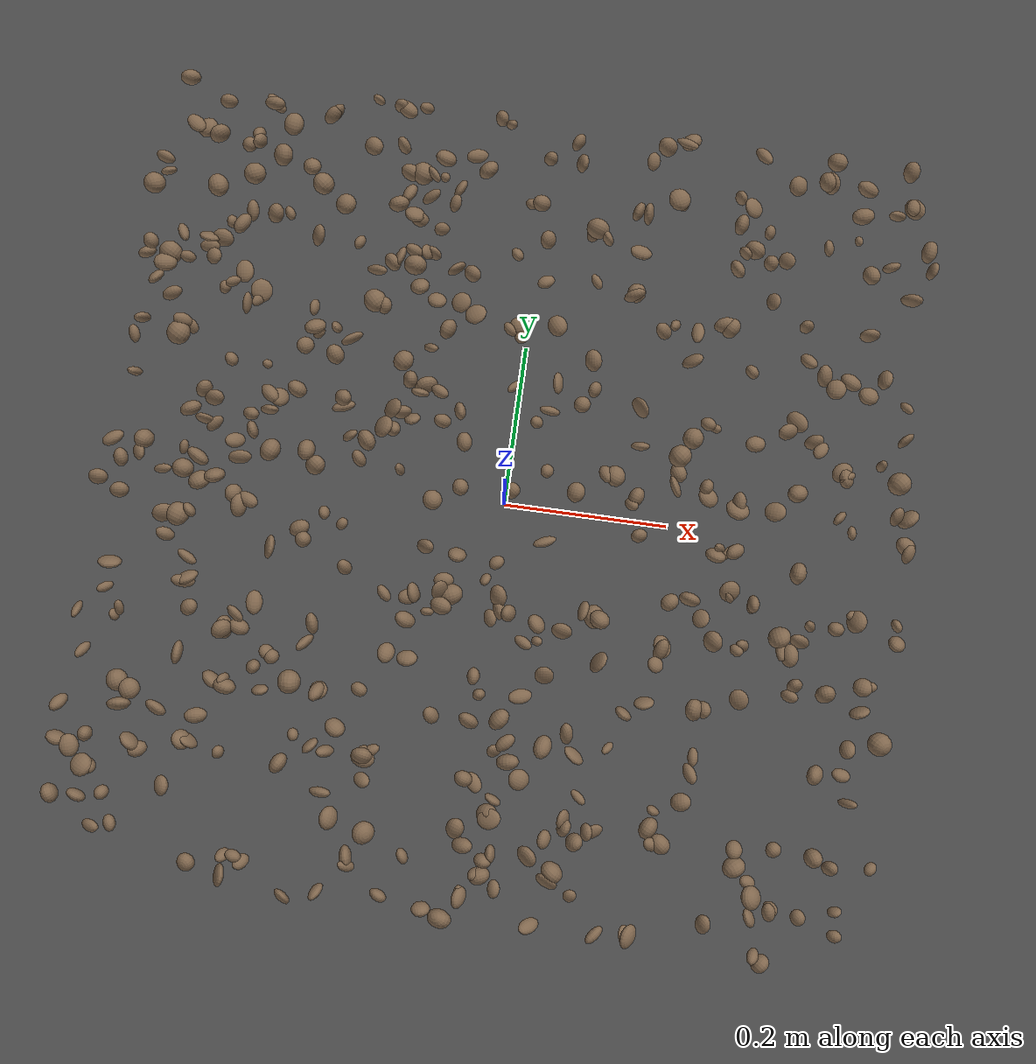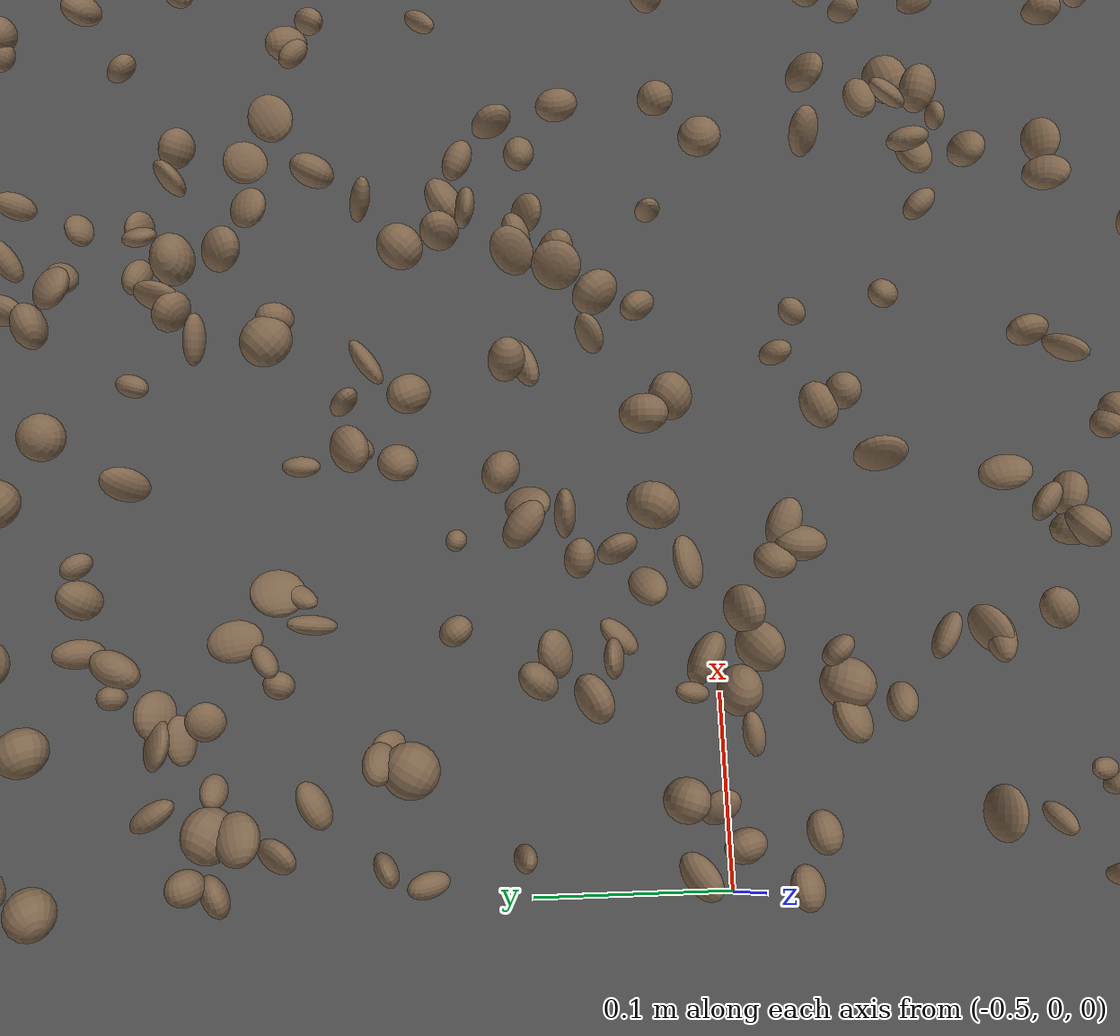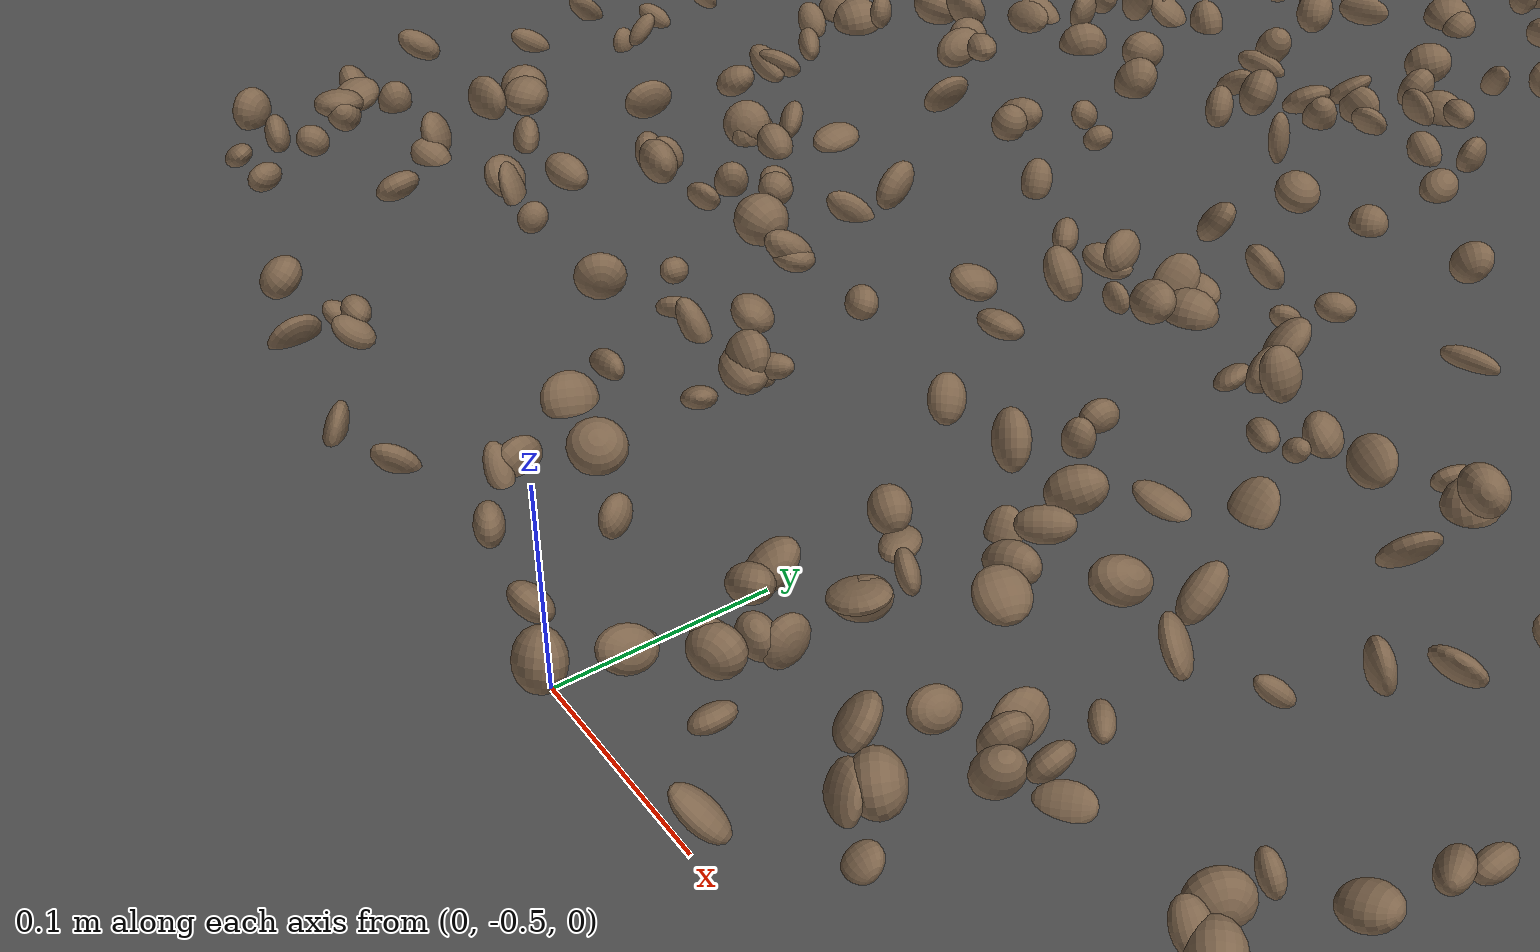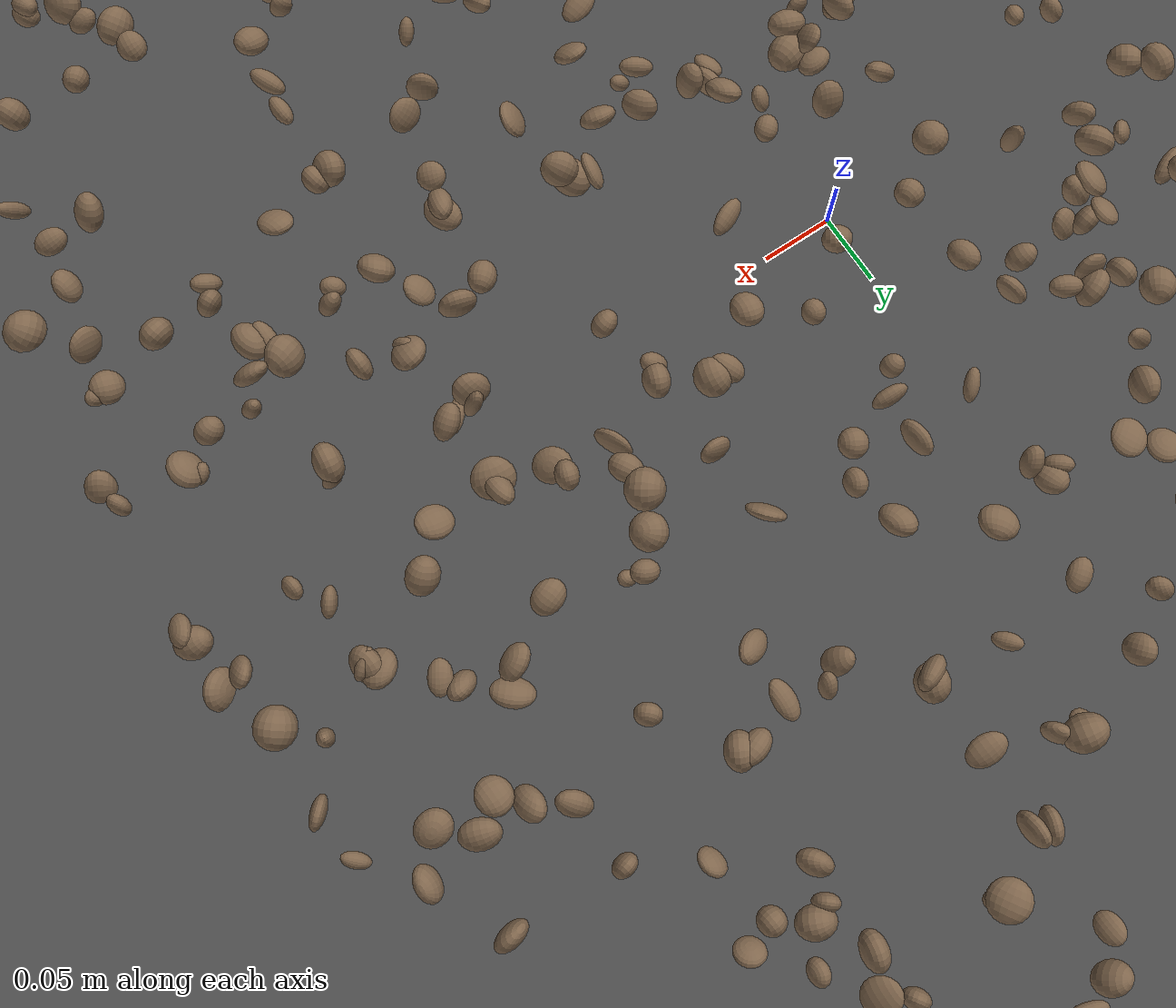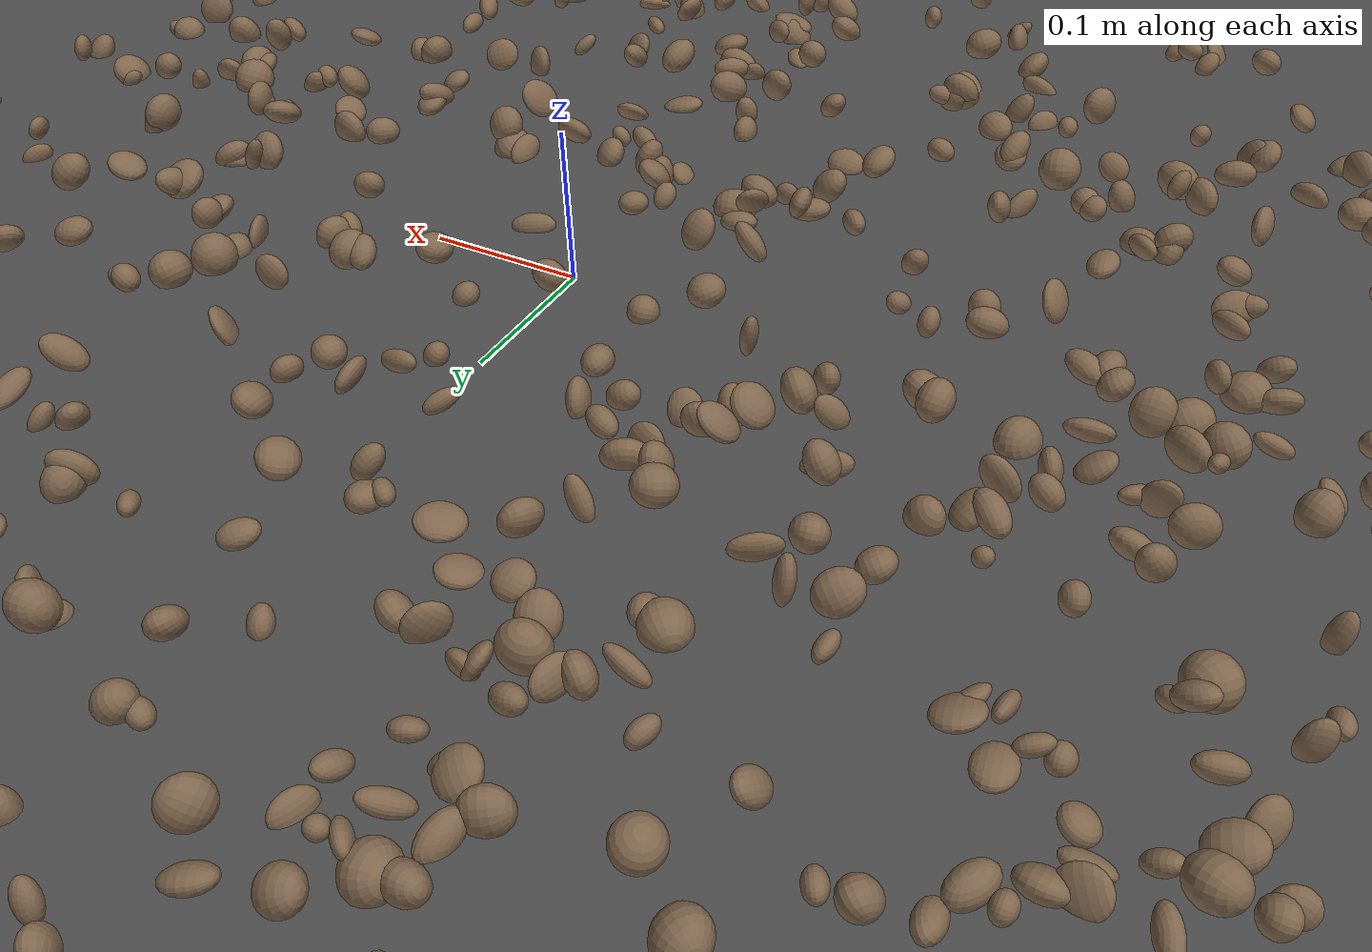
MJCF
<mujoco model="rocky_terrain_scene">
    <compiler angle="radian" inertiafromgeom="true" />
    <option timestep="0.002" gravity="0 0 -9.81" />

    <worldbody>
        <light name="sunlight" pos="5 5 5" dir="-1 -1 -1" diffuse="1 1 1" specular="0.5 0.5 0.5"
            ambient="0.5 0.5 0.5" />

        <geom name="ground_plane" type="plane" size="50 50 0.1" rgba="0.3 0.3 0.3 1" />

        <body name="rocky_terrain_body">

            <geom name="rock1" type="ellipsoid"
                size="0.012656779948914045 0.008592158077966358 0.005492915741358118"
                pos="-0.1597344252763181 -0.4885229630820813 0.003191983491354574"
                quat="0.3232084193160436 0.32986647141787867 0.3382488996296892 0.00867620963638849"
                rgba="0.5 0.4 0.3 1" />
            <geom name="rock2" type="ellipsoid"
                size="0.007945605699883547 0.014233522922651114 0.00892382995548216"
                pos="-0.2872751553409042 0.47228473424276496 0.004838298227512072"
                quat="0.2052471481801577 0.24920379216321303 0.47046933065681124 0.075079728999818"
                rgba="0.5 0.4 0.3 1" />
            <geom name="rock3" type="ellipsoid"
                size="0.013385331679842391 0.012230596726363993 0.01310055072719839"
                pos="-0.4364256581752761 -0.27567593489105335 0.00350951785014283"
                quat="0.2217124141308661 0.18742545660129611 0.25158500274818274 0.3392771265196551"
                rgba="0.5 0.4 0.3 1" />
            <geom name="rock4" type="ellipsoid"
                size="0.010361406220095924 0.010494907450858178 0.006559512658190885"
                pos="-0.40668613755632654 0.26355811935595297 0.01043069861879176"
                quat="0.0971026963093164 0.25139772677353045 0.5317743732040832 0.11972520371307001"
                rgba="0.5 0.4 0.3 1" />
            <geom name="rock5" type="ellipsoid"
                size="0.011327212338188371 0.005321231185972427 0.008666407458373795"
                pos="0.12907060290502803 0.4621491308159018 0.011515446775721942"
                quat="0.15577184710141317 0.3303075716192947 0.2714491678139302 0.24247141346536194"
                rgba="0.5 0.4 0.3 1" />
            <geom name="rock6" type="ellipsoid"
                size="0.014826438211073462 0.013679458659110272 0.01497331041972983"
                pos="-0.4349534038168861 0.15992345557350296 0.00812578029245701"
                quat="0.1500653456129193 0.07708080420522721 0.357686283866262 0.4151675663155915"
                rgba="0.5 0.4 0.3 1" />
            <geom name="rock7" type="ellipsoid"
                size="0.009690908445258875 0.01015970956589933 0.007347247474801308"
                pos="0.09199181784334931 0.1584567234800669 0.0032703214393747836"
                quat="0.5254797559745645 0.12898512383546032 0.325367188942323 0.020167931247652093"
                rgba="0.5 0.4 0.3 1" />
            <geom name="rock8" type="ellipsoid"
                size="0.00889935223507525 0.011953024553652348 0.012792934308896164"
                pos="-0.1003025417849881 0.2093767507874411 0.009716923970736244"
                quat="0.17107400027556377 0.007948864958031033 0.3652148255380018 0.45576230922840344"
                rgba="0.5 0.4 0.3 1" />
            <geom name="rock9" type="ellipsoid"
                size="0.009462378494636915 0.009070567981105317 0.014607672593228052"
                pos="-0.15113141635101024 0.07544765111348262 0.0035350626504592705"
                quat="0.5224805076906838 0.1321261272133926 0.04222304055089625 0.30317032454502746"
                rgba="0.5 0.4 0.3 1" />
            <geom name="rock10" type="ellipsoid"
                size="0.005554376524225203 0.0051645675606478685 0.01354793775349233"
                pos="0.2805939780375728 -0.02165811558662134 0.00029421184092828177"
                quat="0.18018477360548124 0.09878908499773999 0.3640559743689186 0.3569701670278601"
                rgba="0.5 0.4 0.3 1" />
            <geom name="rock11" type="ellipsoid"
                size="0.011204889794771956 0.007142587555670633 0.014709069921736012"
                pos="0.34648430015194764 0.15109148517333437 0.005998441851169279"
                quat="0.31489404480841876 0.36291578284329135 0.06893511761681004 0.25325505473147975"
                rgba="0.5 0.4 0.3 1" />
            <geom name="rock12" type="ellipsoid"
                size="0.006717688412970007 0.009422063156660158 0.006536885593362368"
                pos="0.4672025300924241 -0.16189751146697662 0.0012399208430210068"
                quat="0.19108847882631363 0.37825320762684655 0.41611791454385894 0.014540399002980913"
                rgba="0.5 0.4 0.3 1" />
            <geom name="rock13" type="ellipsoid"
                size="0.012449696349615355 0.014874446832272053 0.005159085553123876"
                pos="0.0318715874373342 -0.37736578567309076 0.00925715320377104"
                quat="0.055254749651894995 0.3731130682225492 0.4963479733587875 0.0752842087667683"
                rgba="0.5 0.4 0.3 1" />
            <geom name="rock14" type="ellipsoid"
                size="0.006918598903032357 0.012249223331573942 0.013373303755026211"
                pos="0.4238936625868869 0.2716612943091913 0.011575420544563815"
                quat="0.14211520716824538 0.32883934008878435 0.42407794393812953 0.10496750880484076"
                rgba="0.5 0.4 0.3 1" />
            <geom name="rock15" type="ellipsoid"
                size="0.009108579465637433 0.014112465310211608 0.012514475360297928"
                pos="0.2716556517890374 -0.13312047351590872 0.012611189332119282"
                quat="0.4747699244105441 0.22641848881753981 0.22724059185115764 0.07157099492075855"
                rgba="0.5 0.4 0.3 1" />
            <geom name="rock16" type="ellipsoid"
                size="0.008069757992862966 0.010775107488614218 0.010210371906665003"
                pos="0.24351604765597445 0.05371767147856976 0.0088510184368787"
                quat="0.058154528397752585 0.0750877603694414 0.5252640545137626 0.34149365671904347"
                rgba="0.5 0.4 0.3 1" />
            <geom name="rock17" type="ellipsoid"
                size="0.011015933865564046 0.00920774241593756 0.013588502719540815"
                pos="0.13580624015654952 -0.390496520186286 0.006938564319975922"
                quat="0.4887980133262226 0.0728040471697961 0.08345413634497302 0.3549438031590082"
                rgba="0.5 0.4 0.3 1" />
            <geom name="rock18" type="ellipsoid"
                size="0.006691494281746151 0.010132815536955518 0.00861156026492862"
                pos="-0.027205175555707894 0.3201149719758105 0.0012138649622763131"
                quat="0.19136402819782744 0.4697604151705152 0.1527307172166451 0.18614483941501225"
                rgba="0.5 0.4 0.3 1" />
            <geom name="rock19" type="ellipsoid"
                size="0.005571432117505245 0.011166424106203231 0.009476858551327568"
                pos="-0.13230146037207913 0.3044340314535069 0.009900843680127353"
                quat="0.41485717758639057 0.11265596498290027 0.1977252533373414 0.2747616040933678"
                rgba="0.5 0.4 0.3 1" />
            <geom name="rock20" type="ellipsoid"
                size="0.007653778514079061 0.01076376606025153 0.011775749725823133"
                pos="-0.49993662173541 -0.034699256455415384 0.014572773332329115"
                quat="0.31119897329109875 0.16027698797281287 0.3607634575172107 0.16776058121887774"
                rgba="0.5 0.4 0.3 1" />
            <geom name="rock21" type="ellipsoid"
                size="0.011552842117515942 0.00941754516859053 0.014754363889361816"
                pos="-0.12760113445310228 -0.32721061005971763 0.00590182180187426"
                quat="0.25534550316966065 0.3066430091760154 0.2147836700775747 0.22322781757674928"
                rgba="0.5 0.4 0.3 1" />
            <geom name="rock22" type="ellipsoid"
                size="0.014913645871581071 0.00788506346205869 0.008314946583298004"
                pos="0.2112782100344286 -0.15154794034042718 0.008226800619355965"
                quat="0.13853471423234093 0.4005281864028649 0.21416785061385785 0.2467692487509364"
                rgba="0.5 0.4 0.3 1" />
            <geom name="rock23" type="ellipsoid"
                size="0.013749153437983587 0.012199734656472418 0.007215582825019294"
                pos="0.2474658885662533 0.04211066921582696 0.004784124632058581"
                quat="0.10095988851359322 0.14937100335006825 0.09590668496090994 0.6537624231754285"
                rgba="0.5 0.4 0.3 1" />
            <geom name="rock24" type="ellipsoid"
                size="0.009832802028469029 0.005027979353494851 0.01033832063242204"
                pos="-0.436206042070315 -0.27942458029906103 0.0013978475137211204"
                quat="0.373262872923086 0.18586359574925154 0.29482284837020906 0.14605068295745327"
                rgba="0.5 0.4 0.3 1" />
            <geom name="rock25" type="ellipsoid"
                size="0.012672285106677722 0.007507523129912369 0.011096684810921083"
                pos="0.4496284987527319 0.21907814210787024 0.006352551386515895"
                quat="0.42775327121962753 0.04870403041649594 0.14201916615016016 0.3815235322137164"
                rgba="0.5 0.4 0.3 1" />
            <geom name="rock26" type="ellipsoid"
                size="0.005546793957854882 0.007548559896774528 0.012242619437016338"
                pos="-0.3700545108704626 0.05123603086081574 0.008525443794398405"
                quat="0.3081830019975435 5.8366773866062557e-05 0.3504399430166461 0.34131868821194433"
                rgba="0.5 0.4 0.3 1" />
            <geom name="rock27" type="ellipsoid"
                size="0.012621551548730936 0.01058159679566354 0.010417835158712342"
                pos="0.42097078338135596 0.3530656229838416 0.0019738914253543314"
                quat="0.2457043910487072 0.18174255049501678 0.38182261512886384 0.19073044332741224"
                rgba="0.5 0.4 0.3 1" />
            <geom name="rock28" type="ellipsoid"
                size="0.014317246945733011 0.008507735179877653 0.014186658562112708"
                pos="0.167916595847736 0.4175512262016434 0.008299920352174117"
                quat="0.15301603343903372 0.20691379405046995 0.3477387287651756 0.2923314437453208"
                rgba="0.5 0.4 0.3 1" />
            <geom name="rock29" type="ellipsoid"
                size="0.01247658761860295 0.00521447200767798 0.011597076042105477"
                pos="0.19779022130219293 -0.21733882928414405 0.014591820354640695"
                quat="0.6121231511764962 0.1626594963054205 0.11937636118719085 0.10584099133089257"
                rgba="0.5 0.4 0.3 1" />
            <geom name="rock30" type="ellipsoid"
                size="0.008381429494404326 0.008808504221594661 0.005223757183951431"
                pos="0.42604958117263647 0.02093354773867684 0.010558226389855038"
                quat="0.3544408584522236 0.12952146828371944 0.26903168722019544 0.2470059860438614"
                rgba="0.5 0.4 0.3 1" />
            <geom name="rock31" type="ellipsoid"
                size="0.013915271865795293 0.007194272881298398 0.011179648825560065"
                pos="-0.0492870408690913 -0.07045251184372248 0.01012529624900321"
                quat="0.43295458727779107 0.1561367604604892 0.35704740665399165 0.053861245607728175"
                rgba="0.5 0.4 0.3 1" />
            <geom name="rock32" type="ellipsoid"
                size="0.01167329960906447 0.006836869803018879 0.013615229678450514"
                pos="-0.296522088572858 0.09586448364620903 0.004121077375223312"
                quat="0.04727038574651898 0.223753380331998 0.47379776602215185 0.2551784678993313"
                rgba="0.5 0.4 0.3 1" />
            <geom name="rock33" type="ellipsoid"
                size="0.012134459088601317 0.01438844033948189 0.014182087151233258"
                pos="-0.1527293676424466 0.2852746446408696 0.013050118608398192"
                quat="0.07133352260367998 0.4397761094445743 0.45169058287084346 0.03719978508090226"
                rgba="0.5 0.4 0.3 1" />
            <geom name="rock34" type="ellipsoid"
                size="0.013212605691388275 0.01294101736892642 0.011009083707355795"
                pos="-0.2517986888795076 0.3534006584268582 0.01096233503882815"
                quat="0.10461333629142062 0.37708335954932587 0.4788914965140086 0.03941180764524496"
                rgba="0.5 0.4 0.3 1" />
            <geom name="rock35" type="ellipsoid"
                size="0.01257270717841611 0.013042039530488977 0.014489666804195708"
                pos="-0.050522190317567994 -0.11880503673858067 0.00023599044510921372"
                quat="0.07042668147374027 0.3260590442880687 0.19374712145997447 0.4097671527782166"
                rgba="0.5 0.4 0.3 1" />
            <geom name="rock36" type="ellipsoid"
                size="0.00982941417834899 0.009755856503366824 0.010859028181975523"
                pos="-0.239704098351882 -0.07671723563959287 0.006306862523702715"
                quat="0.34441009496014297 0.043057449473199 0.07764142082789718 0.534891034738761"
                rgba="0.5 0.4 0.3 1" />
            <geom name="rock37" type="ellipsoid"
                size="0.014881259555451384 0.008645645483289638 0.006316745548621857"
                pos="-0.21603065465788862 0.09523826999051421 0.0022047640141957406"
                quat="0.3484189070831342 0.49818631292464 0.13411667663609775 0.019278103356128062"
                rgba="0.5 0.4 0.3 1" />
            <geom name="rock38" type="ellipsoid"
                size="0.0065331844085121035 0.005404281046715177 0.009913346442422899"
                pos="-0.3769507902380991 0.23351792838573726 0.01146267673855075"
                quat="0.032900057610457924 0.36948729294186705 0.24536795427323563 0.35224469517443946"
                rgba="0.5 0.4 0.3 1" />
            <geom name="rock39" type="ellipsoid"
                size="0.014585877590166815 0.011854247112263936 0.00631044296060174"
                pos="-0.36758047702574803 -0.23322686644580892 0.012455353410679016"
                quat="0.25328113800066737 0.2541431804274594 0.28621398530874986 0.20636169626312345"
                rgba="0.5 0.4 0.3 1" />
            <geom name="rock40" type="ellipsoid"
                size="0.005608670133339064 0.012856625542601023 0.013826740817030569"
                pos="0.26269734181730986 0.4194403730131877 0.0073669797066223145"
                quat="0.034392769711597666 0.6190334574145542 0.018390436138067668 0.32818333673578043"
                rgba="0.5 0.4 0.3 1" />
            <geom name="rock41" type="ellipsoid"
                size="0.014543190662090883 0.0052448173090069395 0.011817631391869702"
                pos="0.4656754985297705 0.444931334715187 0.008297782907696522"
                quat="0.24198704963970077 0.022093408549267498 0.2680722998487865 0.4678472419622452"
                rgba="0.5 0.4 0.3 1" />
            <geom name="rock42" type="ellipsoid"
                size="0.009130414188457642 0.007055595056498533 0.006065808031549979"
                pos="-0.3215309757829947 0.3343431787905591 0.003915822280485445"
                quat="0.15117490949857673 0.2127325384923508 0.32233443550320307 0.31375811650586943"
                rgba="0.5 0.4 0.3 1" />
            <geom name="rock43" type="ellipsoid"
                size="0.007483476682128775 0.007698203346250964 0.011658887539677617"
                pos="-0.09867592605284337 0.12809856340022552 0.012678513629036516"
                quat="0.27840364430873155 0.3271323435420009 0.10162178950538725 0.29284222264388027"
                rgba="0.5 0.4 0.3 1" />
            <geom name="rock44" type="ellipsoid"
                size="0.007042557595431985 0.010245647734858483 0.014194018268754844"
                pos="0.1262104605706289 0.283733929299686 0.01131455605174215"
                quat="0.2565188791255545 0.1378958484204502 0.22922726124427792 0.37635801120971746"
                rgba="0.5 0.4 0.3 1" />
            <geom name="rock45" type="ellipsoid"
                size="0.01426964246656642 0.014673662681774887 0.01354449268371758"
                pos="0.20707459870107903 0.08846790862167087 0.006636918210481463"
                quat="0.2884190935277474 0.3934240358688466 0.11985836525050653 0.19829850535289947"
                rgba="0.5 0.4 0.3 1" />
            <geom name="rock46" type="ellipsoid"
                size="0.014568536985666451 0.009602167912051148 0.012281088069856338"
                pos="-0.3353907477524798 0.4520541022752781 0.006206735810499697"
                quat="0.2261236009056555 0.30031567875342813 0.24536852764627753 0.22819219269463883"
                rgba="0.5 0.4 0.3 1" />
            <geom name="rock47" type="ellipsoid"
                size="0.010781843700941622 0.005272117056693638 0.010477819776959947"
                pos="0.30133911541297587 0.30201220996903866 0.00185176241991368"
                quat="0.34857621660245164 0.18241626302211592 0.09773291762159224 0.3712746027538401"
                rgba="0.5 0.4 0.3 1" />
            <geom name="rock48" type="ellipsoid"
                size="0.011900025475178457 0.012825959161072063 0.00953027557403743"
                pos="-0.4914932473273972 -0.41815030088777705 0.007254519410635724"
                quat="0.22034841226629903 0.152030504458792 0.3297903119013911 0.2978307713735179"
                rgba="0.5 0.4 0.3 1" />
            <geom name="rock49" type="ellipsoid"
                size="0.014253222416351373 0.008962945115001416 0.009166896287037315"
                pos="-0.377907282802425 0.31065119161756294 0.010274145245976623"
                quat="0.5701472785424397 0.04118182103244008 0.04378024818019884 0.3448906522449213"
                rgba="0.5 0.4 0.3 1" />
            <geom name="rock50" type="ellipsoid"
                size="0.010875253782003578 0.011352885816632942 0.013883279402697818"
                pos="0.35440763897758143 0.060172795030709714 0.014246718597657698"
                quat="0.02283864905485016 0.4029925986378264 0.34946994395322767 0.2246988083540957"
                rgba="0.5 0.4 0.3 1" />
            <geom name="rock51" type="ellipsoid"
                size="0.013817380191642675 0.008991477682016736 0.011068655085004977"
                pos="0.08528394701695663 0.19409756041210835 0.008319799345588881"
                quat="0.25993307262133425 0.2128725302422982 0.12874619934227605 0.3984481977940916"
                rgba="0.5 0.4 0.3 1" />
            <geom name="rock52" type="ellipsoid"
                size="0.006320022351581916 0.014360870876249387 0.005854020863878876"
                pos="0.4567156200695778 0.1100547687652772 0.0003415014912189523"
                quat="0.28969201175786746 0.23865581034084923 0.25977618809373987 0.21187598980754352"
                rgba="0.5 0.4 0.3 1" />
            <geom name="rock53" type="ellipsoid"
                size="0.010441504369785581 0.010851501242019192 0.008807939324132624"
                pos="0.27097416321913514 -0.2156895080344423 0.0020722272841922885"
                quat="0.15641597296787021 0.309036154896987 0.28038220092422234 0.2541656712109204"
                rgba="0.5 0.4 0.3 1" />
            <geom name="rock54" type="ellipsoid"
                size="0.010423721475478126 0.01166736737557112 0.014348497869710656"
                pos="0.028209835058670363 -0.2600922320820409 0.007079365090926622"
                quat="0.08526098505546342 0.15219570581805675 0.28096955878390784 0.481573750342572"
                rgba="0.5 0.4 0.3 1" />
            <geom name="rock55" type="ellipsoid"
                size="0.012423576924197892 0.008381777852010365 0.011403009528209891"
                pos="0.05792207128967708 -0.14075144999959177 0.0029505249953429586"
                quat="0.07629606743514647 0.2463164747421328 0.5156116798527897 0.16177577796993103"
                rgba="0.5 0.4 0.3 1" />
            <geom name="rock56" type="ellipsoid"
                size="0.014870414521467056 0.008127562087555537 0.0076227539554124075"
                pos="0.11039012308092855 -0.2658996918336254 0.011970176652273056"
                quat="0.025939977651212507 0.37736008984422864 0.3162241028446319 0.2804758296599269"
                rgba="0.5 0.4 0.3 1" />
            <geom name="rock57" type="ellipsoid"
                size="0.011669162951647993 0.011511516173517092 0.012523600466909108"
                pos="0.3620313429583524 0.4936545401373652 0.00952205669590396"
                quat="0.40908489137272724 0.10148642184774372 0.42729362654990716 0.062135060229621945"
                rgba="0.5 0.4 0.3 1" />
            <geom name="rock58" type="ellipsoid"
                size="0.009641459489811646 0.011341055540258004 0.011427936485022341"
                pos="0.36873195516515456 -0.497880727040246 0.008381119257911178"
                quat="0.05283202885129473 0.1970827934078797 0.3709226762641721 0.3791625014766535"
                rgba="0.5 0.4 0.3 1" />
            <geom name="rock59" type="ellipsoid"
                size="0.013953803595220884 0.01275205929118076 0.014894153992421201"
                pos="-0.1977835508769522 0.2357653915691671 0.0019037565623757546"
                quat="0.36534604013650074 0.34949826867884987 0.11680469254287057 0.1683509986417788"
                rgba="0.5 0.4 0.3 1" />
            <geom name="rock60" type="ellipsoid"
                size="0.00695291404701405 0.013055134642359398 0.012999864781524255"
                pos="-0.4077965395325095 -0.34536501330002156 0.006790154003021347"
                quat="0.38362581930961587 0.3102275496909817 0.0712260440591551 0.23492058694024737"
                rgba="0.5 0.4 0.3 1" />
            <geom name="rock61" type="ellipsoid"
                size="0.005784025319444661 0.009754293773129747 0.008129169720568078"
                pos="0.48986310815956224 -0.08465881236932993 0.013268489898520305"
                quat="0.3226310640852646 0.4659179310566598 0.10096195477577483 0.1104890500823008"
                rgba="0.5 0.4 0.3 1" />
            <geom name="rock62" type="ellipsoid"
                size="0.007998811471890235 0.006545188975207483 0.011454151156309218"
                pos="0.22638676133574887 -0.3807703693312675 0.006068838580709528"
                quat="0.17759947255940656 0.3880628035065666 0.306718306042046 0.12761941789198086"
                rgba="0.5 0.4 0.3 1" />
            <geom name="rock63" type="ellipsoid"
                size="0.012996466007041265 0.008825089930734106 0.005349505055960154"
                pos="0.007968856584626538 -0.3384753188347084 0.0004847833449562061"
                quat="0.056216066134390924 0.31499733949728315 0.6183211620524228 0.010465432315903111"
                rgba="0.5 0.4 0.3 1" />
            <geom name="rock64" type="ellipsoid"
                size="0.008235532314170279 0.012563926336088825 0.014934722213564355"
                pos="-0.3834172740122329 0.007275088932743645 0.01145203226364629"
                quat="0.2933902007241397 0.3390789132923024 0.19427298275217125 0.17325790323138665"
                rgba="0.5 0.4 0.3 1" />
            <geom name="rock65" type="ellipsoid"
                size="0.005169662874763238 0.005875008270823273 0.013589498787872394"
                pos="0.45118615083001634 -0.3017111594442302 0.013647366217834146"
                quat="0.3087981354604913 0.16307640891806055 0.09110195492819728 0.43702350069325085"
                rgba="0.5 0.4 0.3 1" />
            <geom name="rock66" type="ellipsoid"
                size="0.005305465896626683 0.008028994981130584 0.01095965661749954"
                pos="0.41180397799241164 0.03890675390133169 0.000670367543041751"
                quat="0.11266621034281744 0.13654399606728276 0.4732844636714294 0.2775053299184704"
                rgba="0.5 0.4 0.3 1" />
            <geom name="rock67" type="ellipsoid"
                size="0.009590037388175612 0.010162690172146688 0.013160738872847296"
                pos="-0.21708760552574213 0.10439223124413766 0.011698565553644718"
                quat="0.6255136051634645 0.07196595911358526 0.16584874141633 0.13667169430662016"
                rgba="0.5 0.4 0.3 1" />
            <geom name="rock68" type="ellipsoid"
                size="0.013198118394611106 0.012575145111400616 0.01032728255581815"
                pos="0.2510675443770093 0.25773355620723337 0.01081796851570256"
                quat="0.25175746081850375 0.3873630610886748 0.10631277030048158 0.2545667077923399"
                rgba="0.5 0.4 0.3 1" />
            <geom name="rock69" type="ellipsoid"
                size="0.00904529844784661 0.009627291936070231 0.012460318346624213"
                pos="-0.45149168670805573 -0.37988327079841133 0.010691934509661206"
                quat="0.3119561516016587 0.23583329416599924 0.050939404591112805 0.4012711496412293"
                rgba="0.5 0.4 0.3 1" />
            <geom name="rock70" type="ellipsoid"
                size="0.007101943788842182 0.005536621790532985 0.013024912354944147"
                pos="0.039704306414288904 0.12387791913952972 0.004065753186446612"
                quat="0.39350317307814825 0.08107943860029931 0.48717552909130446 0.03824185923024794"
                rgba="0.5 0.4 0.3 1" />
            <geom name="rock71" type="ellipsoid"
                size="0.006974956534615344 0.01465343038094858 0.01083780144793495"
                pos="0.47413694464212 0.32698140770424133 0.0018853496200641616"
                quat="0.1856593153863588 0.3723890317337934 0.3401292988064003 0.10182235407344753"
                rgba="0.5 0.4 0.3 1" />
            <geom name="rock72" type="ellipsoid"
                size="0.008156356028786883 0.014337340731358096 0.010514244281323564"
                pos="0.495713702691301 -0.10536150457646498 0.00023400107147406369"
                quat="0.27459320617752714 0.3622964145100454 0.07576056242940708 0.28734981688302047"
                rgba="0.5 0.4 0.3 1" />
            <geom name="rock73" type="ellipsoid"
                size="0.010323533158752833 0.010316971292164518 0.012157151362445905"
                pos="-0.005517721543112697 0.3899230993717585 0.00605004375550714"
                quat="0.1382125180668813 0.3237659916382506 0.3657983404939756 0.17222314980089248"
                rgba="0.5 0.4 0.3 1" />
            <geom name="rock74" type="ellipsoid"
                size="0.010349063009317531 0.013156989802911346 0.010557325651125955"
                pos="-0.2350364050909063 0.1573031675421942 0.012513240445257942"
                quat="0.3693687347251192 0.06081942801026674 0.3387066994037348 0.2311051378608792"
                rgba="0.5 0.4 0.3 1" />
            <geom name="rock75" type="ellipsoid"
                size="0.009286963557150646 0.007670705436018409 0.009467435097536208"
                pos="-0.26231176496410935 -0.2181311035784277 0.0047081511738556675"
                quat="0.34448117518559884 0.2951191384269015 0.3173595754409288 0.04304011094657083"
                rgba="0.5 0.4 0.3 1" />
            <geom name="rock76" type="ellipsoid"
                size="0.009756571167878089 0.011702922281208956 0.013652764587826365"
                pos="-0.27702894621724283 0.1095786462110373 0.001432046491682286"
                quat="0.11320190265979087 0.49565876627662775 0.281536734752585 0.10960259631099639"
                rgba="0.5 0.4 0.3 1" />
            <geom name="rock77" type="ellipsoid"
                size="0.0053392687261731575 0.006450522654657578 0.0142892129396163"
                pos="0.169500002011166 0.49216290926267103 0.010922420252343091"
                quat="0.163257356880099 0.3948469314901292 0.06087507586724218 0.38102063576252965"
                rgba="0.5 0.4 0.3 1" />
            <geom name="rock78" type="ellipsoid"
                size="0.011024371456940503 0.009673234311975601 0.0075130966582951045"
                pos="-0.00960733058599561 -0.21328702321483084 0.002382108920455436"
                quat="0.28194692904141416 0.20267199354305399 0.35136290756089794 0.16401816985463388"
                rgba="0.5 0.4 0.3 1" />
            <geom name="rock79" type="ellipsoid"
                size="0.010010745900932552 0.007395697856185731 0.006773209072914234"
                pos="-0.26131746924642196 -0.45938797127046416 0.014839348499568259"
                quat="0.08362148862981358 0.00012043961583633682 0.27791672841207476 0.6383413433422754"
                rgba="0.5 0.4 0.3 1" />
            <geom name="rock80" type="ellipsoid"
                size="0.011178263778301502 0.006957400362067585 0.011601697088954366"
                pos="-0.49328418610469404 0.2592588461222939 0.003702612599975895"
                quat="0.5536065346185559 0.013968147155920036 0.28083004313587806 0.15159527508964607"
                rgba="0.5 0.4 0.3 1" />
            <geom name="rock81" type="ellipsoid"
                size="0.008312568084551915 0.008406251203834827 0.007222993752561099"
                pos="-0.38811525192743723 0.2278149693289071 0.0021681335701356813"
                quat="0.24759752982837796 0.2860117373182291 0.2584858542736054 0.20790487857978757"
                rgba="0.5 0.4 0.3 1" />
            <geom name="rock82" type="ellipsoid"
                size="0.005957406641478389 0.013013382927495504 0.014486129890733477"
                pos="-0.46726012835194863 -0.13621952095081102 0.013879629727027129"
                quat="0.19657793412319452 0.304987523090505 0.1575783817519969 0.34085616103430355"
                rgba="0.5 0.4 0.3 1" />
            <geom name="rock83" type="ellipsoid"
                size="0.0052397019395289905 0.013037997612476704 0.014122956658488367"
                pos="0.20615328155873458 0.05053838584820913 0.00113774875348936"
                quat="0.3499310874817112 0.4592149195349503 0.07006237051209202 0.12079162247124652"
                rgba="0.5 0.4 0.3 1" />
            <geom name="rock84" type="ellipsoid"
                size="0.010617905563469861 0.007542366271451053 0.005933841736519394"
                pos="-0.3073293292814564 -0.2575397390666735 0.013835396877604187"
                quat="0.4494644892649885 0.18213034822615917 0.3435309249131309 0.02487423759572132"
                rgba="0.5 0.4 0.3 1" />
            <geom name="rock85" type="ellipsoid"
                size="0.013279612193968521 0.006271588654561705 0.0072969477779878025"
                pos="0.35674936014685377 -0.1329235265553389 0.006292925018753864"
                quat="0.2904264991138205 0.2075238467159751 0.3025375275352165 0.19951212663498782"
                rgba="0.5 0.4 0.3 1" />
            <geom name="rock86" type="ellipsoid"
                size="0.010681398437886895 0.006754867687317461 0.009325591727707467"
                pos="-0.08520496815332534 -0.4808467911080134 0.014418104732664316"
                quat="0.17134922084430784 0.035614015720452676 0.0032169477164433386 0.7898198157187961"
                rgba="0.5 0.4 0.3 1" />
            <geom name="rock87" type="ellipsoid"
                size="0.01423959125950493 0.0075756233105873875 0.011477105892050816"
                pos="-0.47948873211537446 -0.3604028988515383 0.004395882917321595"
                quat="0.16592981525123768 0.26053494683854544 0.2936468734264608 0.27988836448375615"
                rgba="0.5 0.4 0.3 1" />
            <geom name="rock88" type="ellipsoid"
                size="0.008184373064782032 0.005173435454001397 0.013096461612480403"
                pos="-0.41504041702640926 0.27719221744261524 0.0052394258687241515"
                quat="0.1833053151921922 0.28706680991711503 0.17549905950378927 0.3541288153869034"
                rgba="0.5 0.4 0.3 1" />
            <geom name="rock89" type="ellipsoid"
                size="0.009771997800169088 0.008374414160008519 0.011798952063226318"
                pos="-0.36358543942042465 -0.17755839068424917 0.009505574917831447"
                quat="0.231102490102488 0.10771561254369137 0.23954090898899072 0.42164098836483"
                rgba="0.5 0.4 0.3 1" />
            <geom name="rock90" type="ellipsoid"
                size="0.010815720922306187 0.013336270713818387 0.008763267895839913"
                pos="-0.138159361709018 0.13924926854329 0.0070775865215824095"
                quat="0.21435506204626958 0.2358886135821684 0.3237379896606049 0.22601833471095714"
                rgba="0.5 0.4 0.3 1" />
            <geom name="rock91" type="ellipsoid"
                size="0.009058609817125765 0.0055656646667363975 0.014642400438266149"
                pos="0.04987660871312993 -0.229755607365712 0.0008276269841893941"
                quat="0.20955287130645092 0.21165664764388187 0.3381188788121089 0.24067160223755832"
                rgba="0.5 0.4 0.3 1" />
            <geom name="rock92" type="ellipsoid"
                size="0.005419364252342343 0.011578423803761435 0.01246033310476733"
                pos="-0.12375468658885458 0.1251615244615083 0.005214518195433883"
                quat="0.035892892090184245 0.45311421991868517 0.38822032064999057 0.12277256734114005"
                rgba="0.5 0.4 0.3 1" />
            <geom name="rock93" type="ellipsoid"
                size="0.013564825637610498 0.007738023848857552 0.011600452800874968"
                pos="0.4069883419665551 0.09400443499132571 0.010878003783788929"
                quat="0.2895305478487246 0.43387341589795686 0.1455078261808536 0.13108821007246493"
                rgba="0.5 0.4 0.3 1" />
            <geom name="rock94" type="ellipsoid"
                size="0.007940001375673595 0.014026110684677143 0.013183882463567591"
                pos="0.23912463465756606 -0.08562215223441849 0.004204218752671181"
                quat="0.3129612785005213 0.23864788546418222 0.20666224468631553 0.2417285913489809"
                rgba="0.5 0.4 0.3 1" />
            <geom name="rock95" type="ellipsoid"
                size="0.011934956906830003 0.014434202955164038 0.010083713085735559"
                pos="0.41498512646260544 -0.17752038065342302 0.0031703748712499772"
                quat="0.5161333670476302 0.37090488413695544 0.0616053033115348 0.051356445503879626"
                rgba="0.5 0.4 0.3 1" />
            <geom name="rock96" type="ellipsoid"
                size="0.012242828947347888 0.01187721124057077 0.010015170104043226"
                pos="-0.08882159553125968 -0.00784201630627046 0.01285539527039948"
                quat="0.2458192696424921 0.09289103355152974 0.053212620834014866 0.6080770759719633"
                rgba="0.5 0.4 0.3 1" />
            <geom name="rock97" type="ellipsoid"
                size="0.013754220661805858 0.010855175828599335 0.007439386506136781"
                pos="0.3355477598547605 0.13640587104572122 0.009538013090784283"
                quat="0.5678640299456325 0.2142138492977042 0.17482908476911757 0.04309303598754563"
                rgba="0.5 0.4 0.3 1" />
            <geom name="rock98" type="ellipsoid"
                size="0.0141970022291311 0.013122335496490507 0.011315111014706239"
                pos="0.11406253031656843 -0.42869902483733435 0.004969233483690275"
                quat="0.04951048353319178 0.18403534009105357 0.3117134772457286 0.45474069913002596"
                rgba="0.5 0.4 0.3 1" />
            <geom name="rock99" type="ellipsoid"
                size="0.00930161957081109 0.009024965448690896 0.008997803102977618"
                pos="-0.25516058907429895 -0.2230583827124143 0.0057893957061208885"
                quat="0.3972684529289503 0.34688839802340055 0.221247257967419 0.03459589108023004"
                rgba="0.5 0.4 0.3 1" />
            <geom name="rock100" type="ellipsoid"
                size="0.005251345668236952 0.005183315033529723 0.009834195548761561"
                pos="0.4771311148882925 0.18478158928641208 0.014977488530500408"
                quat="0.4151625062917245 0.2807702977707316 0.10430455764298566 0.19976263829455826"
                rgba="0.5 0.4 0.3 1" />
            <geom name="rock101" type="ellipsoid"
                size="0.005146704682367767 0.010520173787737779 0.005444264404418301"
                pos="0.1752016030191892 0.411892717635844 0.0004824027861905161"
                quat="0.18363609181570079 0.2093506495855959 0.34930541169134566 0.2577078469073577"
                rgba="0.5 0.4 0.3 1" />
            <geom name="rock102" type="ellipsoid"
                size="0.014329448787001611 0.009229138854987967 0.007762450900255156"
                pos="0.28452130090124716 0.03856695927163867 0.014216299484256692"
                quat="0.10228843642857328 0.36337274748807086 0.28693617674029204 0.24740263934306383"
                rgba="0.5 0.4 0.3 1" />
            <geom name="rock103" type="ellipsoid"
                size="0.00907030323157291 0.01236459654048419 0.007825836770101569"
                pos="-0.2753406163747103 -0.23801369053103272 0.005671304114154828"
                quat="0.28287449359764905 0.3520590789017776 0.22384737095531626 0.14121905654525718"
                rgba="0.5 0.4 0.3 1" />
            <geom name="rock104" type="ellipsoid"
                size="0.009480850359296219 0.01223225316199512 0.008798334919709917"
                pos="-0.4634262221602762 -0.3440524389715065 0.0030640905224891186"
                quat="0.2697241098906676 0.2876670856439962 0.2557675410546803 0.18684126341065596"
                rgba="0.5 0.4 0.3 1" />
            <geom name="rock105" type="ellipsoid"
                size="0.011346906553710352 0.013169007320309168 0.010413151325689944"
                pos="0.41911800645387054 -0.3706001420823982 0.005657653797815699"
                quat="0.1464536773676534 0.24397372947143622 0.30250955467332713 0.3070630384875833"
                rgba="0.5 0.4 0.3 1" />
            <geom name="rock106" type="ellipsoid"
                size="0.005351401635042171 0.014411381886328612 0.010690562251916858"
                pos="-0.06443395534952023 -0.11616222219119021 0.01080899449417242"
                quat="0.23553023038984774 0.09457976224733414 0.4531682136550641 0.21672179370775405"
                rgba="0.5 0.4 0.3 1" />
            <geom name="rock107" type="ellipsoid"
                size="0.011312589476488645 0.012201479264717806 0.0062215913148227255"
                pos="0.038716436293315226 -0.4173759008518515 0.01096880353412463"
                quat="0.322641695385338 0.17035257638510506 0.308235594843565 0.19877013338599198"
                rgba="0.5 0.4 0.3 1" />
            <geom name="rock108" type="ellipsoid"
                size="0.006100811677023739 0.007455092601413202 0.010331837373917636"
                pos="-0.44148323822885127 0.2605419507223724 0.0027031187621650125"
                quat="0.25695206330351206 0.20051797189311238 0.466473158426056 0.07605680637731962"
                rgba="0.5 0.4 0.3 1" />
            <geom name="rock109" type="ellipsoid"
                size="0.01430260566677935 0.01450460035384962 0.01211646518250145"
                pos="-0.2985087995887752 0.028915334619838418 0.0004196020886215634"
                quat="0.19139464670154083 0.44823986889571954 0.10610764377892204 0.2542578406238175"
                rgba="0.5 0.4 0.3 1" />
            <geom name="rock110" type="ellipsoid"
                size="0.006851864119838446 0.006548051732789738 0.008403228955860046"
                pos="-0.017753029312726043 0.3882328889179033 0.0027878767873552907"
                quat="0.27539448106901665 0.3057720555325121 0.07854116038347482 0.34029230301499647"
                rgba="0.5 0.4 0.3 1" />
            <geom name="rock111" type="ellipsoid"
                size="0.007549102572671148 0.009261048902433459 0.01290112338908508"
                pos="0.3516269218283601 0.22836689895499473 0.011819447619761943"
                quat="0.38258569170625367 0.2702015687000035 0.004899889915529099 0.3423128496782137"
                rgba="0.5 0.4 0.3 1" />
            <geom name="rock112" type="ellipsoid"
                size="0.006781406875471097 0.0056989106712796896 0.01420522379639674"
                pos="-0.19936380070018422 0.27277057368705304 0.011508004481594052"
                quat="0.14836225172807663 0.3130760555845459 0.06212670347465498 0.47643498921272254"
                rgba="0.5 0.4 0.3 1" />
            <geom name="rock113" type="ellipsoid"
                size="0.012999550071476209 0.0065510943415041665 0.005789696082387795"
                pos="-0.12833279436561473 -0.45445967802771714 0.0032940832224924257"
                quat="0.033345245341153545 0.28151222123064656 0.03220802629741393 0.6529345071307859"
                rgba="0.5 0.4 0.3 1" />
            <geom name="rock114" type="ellipsoid"
                size="0.011834925425959465 0.0069976628116493154 0.012729264293145161"
                pos="0.08922843614475273 -0.1453279142955387 0.011242050754180416"
                quat="0.1570892209976616 0.4373372033278307 0.0830807217653771 0.3224928539091305"
                rgba="0.5 0.4 0.3 1" />
            <geom name="rock115" type="ellipsoid"
                size="0.006146307367445213 0.00666758193642324 0.012173257044299904"
                pos="-0.48385072041151866 -0.24558658342314754 0.0040582698964266055"
                quat="0.08447215809003344 0.11622343891930419 0.5067684383771394 0.29253596461352305"
                rgba="0.5 0.4 0.3 1" />
            <geom name="rock116" type="ellipsoid"
                size="0.008447226709967169 0.011721893056792505 0.009016037290162796"
                pos="-0.12606711843406104 -0.320884853452424 0.0063104475687336585"
                quat="0.36103384860780646 0.28118460436820536 0.05579962402290829 0.3019819230010799"
                rgba="0.5 0.4 0.3 1" />
            <geom name="rock117" type="ellipsoid"
                size="0.012997235541288028 0.0052716319062745725 0.013863382208011591"
                pos="-0.41706220854527 0.28993713994397474 0.0038530944076687196"
                quat="0.2632778674192612 0.11866065789386371 0.49652848361674673 0.12153299107012834"
                rgba="0.5 0.4 0.3 1" />
            <geom name="rock118" type="ellipsoid"
                size="0.005692603969640362 0.005630633740026454 0.007669545546377669"
                pos="0.060992975674650785 -0.16122580479448279 0.006036301504200749"
                quat="0.12906618346792942 0.26152184237704945 0.0093591168211988 0.6000528573338223"
                rgba="0.5 0.4 0.3 1" />
            <geom name="rock119" type="ellipsoid"
                size="0.009185121726239582 0.009795923666269447 0.007282100486903722"
                pos="0.28447272497558673 0.20771697228821795 0.0029318931663151215"
                quat="0.24046612094870923 0.05588514190856163 0.34863061533232054 0.35501812181040854"
                rgba="0.5 0.4 0.3 1" />
            <geom name="rock120" type="ellipsoid"
                size="0.00875446589042805 0.007125162408034975 0.01332076436450929"
                pos="-0.4506793252496769 0.20851852529816428 0.010525554081411386"
                quat="0.02582635540696846 0.30758493778745 0.1849328161897147 0.4816558906158669"
                rgba="0.5 0.4 0.3 1" />
            <geom name="rock121" type="ellipsoid"
                size="0.010772934756588831 0.006007249208228876 0.011753521301879236"
                pos="0.08319949119656711 0.35537691772263 0.006391748354121747"
                quat="0.031191670314729626 0.32707751746094627 0.629660467336991 0.012070344887333096"
                rgba="0.5 0.4 0.3 1" />
            <geom name="rock122" type="ellipsoid"
                size="0.013011086862896627 0.01375156711552036 0.008549939421422553"
                pos="0.25068078832680685 0.3968653029703648 0.003559950922395399"
                quat="0.15207740961548205 0.3875926549572713 0.05311720034644446 0.40721273508080214"
                rgba="0.5 0.4 0.3 1" />
            <geom name="rock123" type="ellipsoid"
                size="0.009315763690768381 0.012426552246871692 0.006762298938550307"
                pos="0.2462321230917135 0.4319885471595031 0.004162118599882276"
                quat="0.155680031372696 0.1909584602951185 0.3211717599293707 0.33218974840281484"
                rgba="0.5 0.4 0.3 1" />
            <geom name="rock124" type="ellipsoid"
                size="0.00617322885986567 0.009632286425806734 0.008003509791481195"
                pos="0.023429667322870773 -0.44125826905176047 0.01498614809918728"
                quat="0.19453096205922085 0.18526827466504958 0.1519591913862312 0.46824157188949844"
                rgba="0.5 0.4 0.3 1" />
            <geom name="rock125" type="ellipsoid"
                size="0.014722745250279022 0.012304040350246001 0.013367425081801717"
                pos="0.12625686572701855 -0.12222798040245064 0.00014707935041620155"
                quat="0.12201758232404805 0.3583416466144481 0.43490519956534435 0.08473557149615953"
                rgba="0.5 0.4 0.3 1" />
            <geom name="rock126" type="ellipsoid"
                size="0.014120766380511757 0.008511539301939767 0.013093444801569439"
                pos="-0.15775535390007478 -0.4027817807710543 0.0021188241363092795"
                quat="0.17306776943325197 0.38566043196245836 0.35810435698558474 0.08316744161870496"
                rgba="0.5 0.4 0.3 1" />
            <geom name="rock127" type="ellipsoid"
                size="0.0058446081185773106 0.013407367509129409 0.011437409220951536"
                pos="0.31028396654707047 -0.19801528199750518 0.013195800090268448"
                quat="0.452247171159275 0.02793478532672875 0.3580070783545026 0.1618109651594936"
                rgba="0.5 0.4 0.3 1" />
            <geom name="rock128" type="ellipsoid"
                size="0.005381123493561654 0.013957716112384382 0.0058686993451296295"
                pos="0.26783245207015005 -0.019354102120570427 0.009032654826735353"
                quat="0.19725673490068213 0.044040680911822054 0.3642106187969861 0.3944919653905098"
                rgba="0.5 0.4 0.3 1" />
            <geom name="rock129" type="ellipsoid"
                size="0.008180901785002264 0.008602160960932064 0.009593876479095344"
                pos="0.3754138030148716 -0.43591518684644726 0.0024632708712631376"
                quat="0.451831880867775 0.2865152994649436 0.05896693911114805 0.20268588055613349"
                rgba="0.5 0.4 0.3 1" />
            <geom name="rock130" type="ellipsoid"
                size="0.010484130645158251 0.01423518678116496 0.009273260446441103"
                pos="0.49006535238103965 0.39240135288657796 0.004683177299527748"
                quat="0.43730448162600544 0.07148744059669543 0.47740485491318063 0.013803222864118612"
                rgba="0.5 0.4 0.3 1" />
            <geom name="rock131" type="ellipsoid"
                size="0.007144342455132672 0.005487375762284743 0.005707664985582787"
                pos="0.2477565985903849 0.12976004172270938 0.002578444000396238"
                quat="0.26561527297457516 0.07000693373223417 0.6601840826634519 0.004193710629738884"
                rgba="0.5 0.4 0.3 1" />
            <geom name="rock132" type="ellipsoid"
                size="0.009879427631405393 0.00817883224833429 0.008032952971987898"
                pos="0.23688208966123014 0.13315244510668256 0.007662838558922837"
                quat="0.13672919767461178 0.059241063978099286 0.5719518157590584 0.23207792258823057"
                rgba="0.5 0.4 0.3 1" />
            <geom name="rock133" type="ellipsoid"
                size="0.008822746792803048 0.009713717952386649 0.009286574576327533"
                pos="0.3702600780421246 -0.3668521165198836 0.010659251628515703"
                quat="0.2523775010417901 0.037196946330214815 0.3559246571546126 0.35450089547338254"
                rgba="0.5 0.4 0.3 1" />
            <geom name="rock134" type="ellipsoid"
                size="0.007455015549259885 0.010714298810750707 0.005475465060815331"
                pos="0.2839260814971283 -0.07582940063370258 0.012715106722018633"
                quat="0.3221603007108376 0.024196201614179465 0.389175856736131 0.26446764093885194"
                rgba="0.5 0.4 0.3 1" />
            <geom name="rock135" type="ellipsoid"
                size="0.009986480509886292 0.012641623748799593 0.011193261225621334"
                pos="-0.3031983795486447 0.3989506994063746 0.006060231522616615"
                quat="0.048180126946627856 0.35396664404198863 0.2358521315614469 0.36200109744993664"
                rgba="0.5 0.4 0.3 1" />
            <geom name="rock136" type="ellipsoid"
                size="0.007293933765358261 0.008713368189057387 0.0051144886944056046"
                pos="-0.45381591997182236 -0.1986364161085935 0.0027226143760698818"
                quat="0.27352623341510485 0.15137736192974638 0.28413128391784553 0.2909651207373033"
                rgba="0.5 0.4 0.3 1" />
            <geom name="rock137" type="ellipsoid"
                size="0.005016432932455944 0.008355624551451576 0.009125671608070336"
                pos="-0.23077423538555497 0.4974364319186395 0.011308700160534304"
                quat="0.07250234064355009 0.5248365717632157 0.33285241354168504 0.0698086740515491"
                rgba="0.5 0.4 0.3 1" />
            <geom name="rock138" type="ellipsoid"
                size="0.009537644666214947 0.012196634271860376 0.009125344232191912"
                pos="-0.060546601940981826 0.07087410482326195 0.0030112608922445478"
                quat="0.6783196422127725 0.019469576177299466 0.21007444810570605 0.09213633350422197"
                rgba="0.5 0.4 0.3 1" />
            <geom name="rock139" type="ellipsoid"
                size="0.007712478822240722 0.007334875527235239 0.009253714384767762"
                pos="0.02548149264316424 0.10762796986515921 0.0023453539216347755"
                quat="0.13989062716446055 0.2847921781707234 0.4974637469032551 0.07785344776156099"
                rgba="0.5 0.4 0.3 1" />
            <geom name="rock140" type="ellipsoid"
                size="0.009513572767605213 0.011155849216524618 0.013580795395263447"
                pos="-0.17629173194754 0.4082789055003996 0.0052682843987453465"
                quat="0.25104186175977034 0.29656960427054246 0.32533756100634686 0.12705097296334036"
                rgba="0.5 0.4 0.3 1" />
            <geom name="rock141" type="ellipsoid"
                size="0.011970443306865034 0.005879718343317225 0.013271862437884686"
                pos="0.3300719292011418 0.034354703971797296 0.011916851258289637"
                quat="0.3082847113105402 0.21365276693741023 0.19061896600195785 0.2874435557500916"
                rgba="0.5 0.4 0.3 1" />
            <geom name="rock142" type="ellipsoid"
                size="0.006844992832790514 0.008416932622135746 0.006483939527163864"
                pos="-0.19447051828742745 -0.05183231320836035 0.010163834408880598"
                quat="0.2298969588864227 0.21584262091771725 0.4684946818090169 0.08576573838684322"
                rgba="0.5 0.4 0.3 1" />
            <geom name="rock143" type="ellipsoid"
                size="0.010803496677074611 0.010101168590627579 0.01472969116554336"
                pos="0.40036011172689145 0.42472944528791223 0.013404415891071652"
                quat="0.2579131721209676 0.1354158466837792 0.3884017592024402 0.21826922199281307"
                rgba="0.5 0.4 0.3 1" />
            <geom name="rock144" type="ellipsoid"
                size="0.010067645305963706 0.011164187037373596 0.014040907674691242"
                pos="0.49529799350478143 0.01460343636002992 0.0023941473599750833"
                quat="0.13253810750890432 0.5317237894559308 0.07526852352462932 0.26046957951053556"
                rgba="0.5 0.4 0.3 1" />
            <geom name="rock145" type="ellipsoid"
                size="0.009164093444878485 0.009135726370336267 0.007515166697870886"
                pos="-0.3637060587232481 0.13552432450622187 0.006299553359601812"
                quat="0.2942171595991535 0.06598611769792653 0.3227183230746372 0.3170783996282827"
                rgba="0.5 0.4 0.3 1" />
            <geom name="rock146" type="ellipsoid"
                size="0.008450526946577785 0.007879848153511955 0.013453343783488055"
                pos="0.03933158840545703 -0.2867133788871741 0.008087646304487018"
                quat="0.018190265377429096 0.26350454191670725 0.27905852902121214 0.4392466636846516"
                rgba="0.5 0.4 0.3 1" />
            <geom name="rock147" type="ellipsoid"
                size="0.010281116612741337 0.008837059526582014 0.005891964135125463"
                pos="0.3630235082887423 0.3798152238179294 0.006077676329062473"
                quat="0.23403979972066558 0.22823451847835433 0.1791364090178792 0.35858927278310093"
                rgba="0.5 0.4 0.3 1" />
            <geom name="rock148" type="ellipsoid"
                size="0.014710754225736259 0.009218443443202776 0.007463287769698937"
                pos="-0.17449641392108728 0.381909037298658 0.0022436033871708672"
                quat="0.27172390861766416 0.32482475160728524 0.3201677404333488 0.08328359934170197"
                rgba="0.5 0.4 0.3 1" />
            <geom name="rock149" type="ellipsoid"
                size="0.011753718545396794 0.01331957772491826 0.008639421106665088"
                pos="0.4294234228108329 0.1941010265590143 0.012336266869484932"
                quat="0.37015603596560964 0.0019098493842059747 0.14884355448418696 0.47909056016599744"
                rgba="0.5 0.4 0.3 1" />
            <geom name="rock150" type="ellipsoid"
                size="0.013369722343386639 0.009043011566771316 0.005177499791297632"
                pos="0.11234276508198571 -0.11706008212061825 0.003754742912769422"
                quat="0.2534370137680275 0.2974530899224126 0.3342714133019742 0.11483848300758559"
                rgba="0.5 0.4 0.3 1" />
            <geom name="rock151" type="ellipsoid"
                size="0.008766508020318167 0.005644956442917558 0.014363660639839494"
                pos="0.09458740710365421 -0.4920734082856999 0.011293880979914706"
                quat="0.15469213582074268 0.185467236829014 0.4591823623609867 0.2006582649892566"
                rgba="0.5 0.4 0.3 1" />
            <geom name="rock152" type="ellipsoid"
                size="0.010613428853575729 0.010641118501147639 0.005631799222142207"
                pos="0.3122512685840553 0.35657906479614176 0.004985834786967479"
                quat="0.12240097571189285 0.06409405554527049 0.6464365026649465 0.16706846607789017"
                rgba="0.5 0.4 0.3 1" />
            <geom name="rock153" type="ellipsoid"
                size="0.013458109201203917 0.01117733277136025 0.01250057198713287"
                pos="0.13020630281993972 0.05181159418713843 0.012896485846488994"
                quat="0.2619660684777789 0.2771335278249548 0.34649626641460546 0.11440413728266079"
                rgba="0.5 0.4 0.3 1" />
            <geom name="rock154" type="ellipsoid"
                size="0.006646960804717489 0.012032897832805298 0.01124275079670658"
                pos="-0.32301805047686183 0.04980416861560499 0.006918015126382609"
                quat="0.4169695169795063 0.4090237872820906 0.10794702388991591 0.06605967184848724"
                rgba="0.5 0.4 0.3 1" />
            <geom name="rock155" type="ellipsoid"
                size="0.013361324577490133 0.011477648219088116 0.010497948476972191"
                pos="-0.25136339357441095 0.032438383518326064 0.0148054932460379"
                quat="0.3143484089356372 0.19262157991932966 0.27567638584713083 0.21735362529790228"
                rgba="0.5 0.4 0.3 1" />
            <geom name="rock156" type="ellipsoid"
                size="0.014414675353077173 0.008334449450100057 0.01019597274837638"
                pos="0.37398221647769403 0.21325088003018544 0.008013714846377864"
                quat="0.04603823200828388 0.35928141452143636 0.31966441134494533 0.2750159421253345"
                rgba="0.5 0.4 0.3 1" />
            <geom name="rock157" type="ellipsoid"
                size="0.005625186796676571 0.01418181833857141 0.009000379581217657"
                pos="-0.4834909840898248 0.17314430158384086 0.006965985731309879"
                quat="0.2165835171662879 0.17325327409153893 0.2559544876889821 0.3542087210531912"
                rgba="0.5 0.4 0.3 1" />
            <geom name="rock158" type="ellipsoid"
                size="0.011392084502046951 0.013515386897288699 0.011491134645343227"
                pos="0.12837279911243515 0.2887046621842596 0.0059863182802149225"
                quat="0.19522725647262162 0.5399880069469503 0.036779916702281715 0.2280048198781464"
                rgba="0.5 0.4 0.3 1" />
            <geom name="rock159" type="ellipsoid"
                size="0.013434048907694382 0.0077760165742701455 0.0125243018048922"
                pos="0.26382917315936116 -0.028576518980111487 0.008888489402458323"
                quat="0.30786262475620474 0.11285582395298706 0.4935645942165807 0.08571695707422747"
                rgba="0.5 0.4 0.3 1" />
            <geom name="rock160" type="ellipsoid"
                size="0.010801943914896101 0.009517117620076948 0.012821741017096357"
                pos="-0.3005767940238584 -0.1929363019532193 0.0021505784858047382"
                quat="0.39355764822918315 0.1393486860724673 0.45481614563199035 0.012277520066359151"
                rgba="0.5 0.4 0.3 1" />
            <geom name="rock161" type="ellipsoid"
                size="0.014764636682400793 0.010697316936804747 0.010311846782533642"
                pos="0.08431869565976613 -0.2853281331960772 0.00926765108024237"
                quat="0.44604328178809977 0.05864529079337223 0.19019090809569622 0.3051205193228318"
                rgba="0.5 0.4 0.3 1" />
            <geom name="rock162" type="ellipsoid"
                size="0.01441641302003897 0.0094068017817945 0.012727427580791173"
                pos="-0.12878228308351358 -0.3245031873354486 0.010758701158426968"
                quat="0.08976143202961627 0.5464346961503741 0.03341862184019688 0.3303852499798128"
                rgba="0.5 0.4 0.3 1" />
            <geom name="rock163" type="ellipsoid"
                size="0.005993085051758542 0.0058743261166822 0.006111441049181556"
                pos="-0.13179682582291807 0.40562049707017434 0.010582996018275958"
                quat="0.11439441312535975 0.3997183571505888 0.09127949627623859 0.39460773344781286"
                rgba="0.5 0.4 0.3 1" />
            <geom name="rock164" type="ellipsoid"
                size="0.00991950437150408 0.006273788782493922 0.010024398891723648"
                pos="0.20628390846610145 -0.17021570816117026 0.011942844091956896"
                quat="0.3045881319874451 0.3012772331604345 0.2844726319559236 0.10966200289619686"
                rgba="0.5 0.4 0.3 1" />
            <geom name="rock165" type="ellipsoid"
                size="0.01432322221743991 0.014612213434927877 0.009280604134264726"
                pos="0.35011540314690226 -0.4250965650641324 0.009467386335246193"
                quat="0.381329757811996 0.09193828765353777 0.18105426081155748 0.3456776937229087"
                rgba="0.5 0.4 0.3 1" />
            <geom name="rock166" type="ellipsoid"
                size="0.013311790705891453 0.00522439702816715 0.007139011881525381"
                pos="-0.341366520806604 0.21836203468224424 0.005108828649605527"
                quat="0.24676952627518264 0.4270767774742623 0.2823594911083428 0.04379420514221227"
                rgba="0.5 0.4 0.3 1" />
            <geom name="rock167" type="ellipsoid"
                size="0.00556992415102029 0.014326038022625217 0.011423852154270043"
                pos="0.07549084440937437 -0.20138314275437785 0.002034532233491838"
                quat="0.35593636619148084 0.11598775771693558 0.3473600626620587 0.18071581342952492"
                rgba="0.5 0.4 0.3 1" />
            <geom name="rock168" type="ellipsoid"
                size="0.014619677121389542 0.005689081680386967 0.013503883242466163"
                pos="-0.3404711848747962 0.22764576784985524 0.007177115949144891"
                quat="0.16667875950819622 0.2877423143381837 0.27333228548803074 0.27224664066558946"
                rgba="0.5 0.4 0.3 1" />
            <geom name="rock169" type="ellipsoid"
                size="0.007790079116701163 0.009855222502231217 0.010109214592653352"
                pos="0.16800525538788103 -0.01752370178988827 0.012910165215045628"
                quat="0.194658587820138 0.2347380841470937 0.43561134872500984 0.13499197930775847"
                rgba="0.5 0.4 0.3 1" />
            <geom name="rock170" type="ellipsoid"
                size="0.011510815480651061 0.007326095390891603 0.010809924903672741"
                pos="-0.19205288057874614 -0.2549284309163379 0.0075272878076674205"
                quat="0.27696095740101806 0.15061148008967082 0.32740335727953174 0.24502420522977933"
                rgba="0.5 0.4 0.3 1" />
            <geom name="rock171" type="ellipsoid"
                size="0.010063601522386768 0.005625368610328711 0.014782808087768572"
                pos="-0.30453012013291225 0.07665686562195351 0.013395413134290275"
                quat="0.7502296909386579 0.010151330261960322 0.23731956747369604 0.0022994113256857513"
                rgba="0.5 0.4 0.3 1" />
            <geom name="rock172" type="ellipsoid"
                size="0.00965470140444602 0.011103024600712523 0.013593381468411998"
                pos="-0.06041992450189315 -0.13458442874860732 0.007733789992733054"
                quat="0.4229182701537538 0.16555528885008766 0.29650066879269443 0.11502577220346426"
                rgba="0.5 0.4 0.3 1" />
            <geom name="rock173" type="ellipsoid"
                size="0.009612566942607603 0.00505667910305342 0.01110804940223336"
                pos="-0.13958755862435945 0.30320911788950244 0.014707711601392818"
                quat="0.05189799266375271 0.3415506820888685 0.4347984514589226 0.17175287378845616"
                rgba="0.5 0.4 0.3 1" />
            <geom name="rock174" type="ellipsoid"
                size="0.014452238728621041 0.0060089621722067155 0.011153959615858876"
                pos="-0.3652679509591219 0.24945186296016642 0.008003001943391085"
                quat="0.2144192000850158 0.24180342186101678 0.2655224209276404 0.27825495712632703"
                rgba="0.5 0.4 0.3 1" />
            <geom name="rock175" type="ellipsoid"
                size="0.008887245337493356 0.006642309356028866 0.006776518370958138"
                pos="0.4864928297800887 -0.3736569002442005 0.008405486881635262"
                quat="0.40845912452941924 0.24444957695929959 0.21483279834034527 0.13225850017093582"
                rgba="0.5 0.4 0.3 1" />
            <geom name="rock176" type="ellipsoid"
                size="0.0065686288789453765 0.01005190476921242 0.014991572899277397"
                pos="0.377239844379754 -0.11869239016386302 0.004147920119713135"
                quat="0.21753044961326803 0.32107357843796275 0.40981907918517324 0.051576892763595894"
                rgba="0.5 0.4 0.3 1" />
            <geom name="rock177" type="ellipsoid"
                size="0.01151944988680613 0.010789893938620204 0.005274069221015935"
                pos="0.49316982658959607 0.3643325549153831 0.014986195139351038"
                quat="0.16941993318797385 0.3989593108802798 0.1473555763348847 0.2842651795968616"
                rgba="0.5 0.4 0.3 1" />
            <geom name="rock178" type="ellipsoid"
                size="0.011845006039882228 0.00642173179096587 0.011231440773857976"
                pos="-0.11968659584432106 0.24548610672141535 0.006053658230742984"
                quat="0.0043802725388663215 0.033386810947690825 0.5934689717967149 0.36876394471672785"
                rgba="0.5 0.4 0.3 1" />
            <geom name="rock179" type="ellipsoid"
                size="0.014908599137726422 0.00840467275596143 0.014495152898581606"
                pos="0.2839317438375618 0.03068043865149972 0.011785247842228225"
                quat="0.026093376676790993 0.0784701859059758 0.5874586499486654 0.3079777874685678"
                rgba="0.5 0.4 0.3 1" />
            <geom name="rock180" type="ellipsoid"
                size="0.006215771983461562 0.005347824153332965 0.005057751110153981"
                pos="0.39980388082589036 0.39403445463397835 0.006576394821061581"
                quat="0.23206323971660997 0.2045817813252688 0.20434561194225603 0.3590093670158653"
                rgba="0.5 0.4 0.3 1" />
            <geom name="rock181" type="ellipsoid"
                size="0.005538041146255819 0.013462504038625478 0.008710837767259755"
                pos="0.44379780212215114 0.43147449405275284 0.011648195544132663"
                quat="0.3377346408492491 0.1278107934185294 0.14703732542259398 0.38741724030962754"
                rgba="0.5 0.4 0.3 1" />
            <geom name="rock182" type="ellipsoid"
                size="0.0067104479501554105 0.011364862482982465 0.005725130919825659"
                pos="0.1823158247813046 0.2545363184012479 0.0024185389231702005"
                quat="0.22668830620327923 0.2693172283147493 0.141971654297259 0.36202281118471247"
                rgba="0.5 0.4 0.3 1" />
            <geom name="rock183" type="ellipsoid"
                size="0.012430577541002885 0.005674790906168978 0.009641465288965752"
                pos="-0.11090227506791472 0.3974983838485885 0.0007188477629315792"
                quat="0.4991389736779987 0.07870325247278817 0.0861919678048031 0.33596580604441006"
                rgba="0.5 0.4 0.3 1" />
            <geom name="rock184" type="ellipsoid"
                size="0.012494788857128184 0.009303364538987283 0.01111392419374924"
                pos="0.084705053720043 0.025399603715559715 0.01227839398392509"
                quat="0.26997033748645594 0.2630004197307543 0.17948184691725577 0.28754739586553396"
                rgba="0.5 0.4 0.3 1" />
            <geom name="rock185" type="ellipsoid"
                size="0.011047351457688495 0.014171596638046454 0.012053495311867635"
                pos="-0.23907593801369487 0.016697326910008026 0.006052249100910226"
                quat="0.3591157125906009 0.30900454632522123 0.2767349836211189 0.055144757463058997"
                rgba="0.5 0.4 0.3 1" />
            <geom name="rock186" type="ellipsoid"
                size="0.009576765511724997 0.008628820485631449 0.013453100139880679"
                pos="0.24248802288562965 0.2606433724593248 0.012763515988931235"
                quat="0.051524351837422884 0.3336955818105332 0.17001395899593866 0.4447661073561053"
                rgba="0.5 0.4 0.3 1" />
            <geom name="rock187" type="ellipsoid"
                size="0.012152761666492828 0.009929554094390954 0.009704112369190668"
                pos="0.20823248150075124 0.0683393907649924 2.7996508549871236e-06"
                quat="0.14904039782410056 0.217632385750874 0.3463742157307 0.2869530006943255"
                rgba="0.5 0.4 0.3 1" />
            <geom name="rock188" type="ellipsoid"
                size="0.009527422650265127 0.013662115174886871 0.008724650201468103"
                pos="0.004780013457392984 -0.4113610798507734 0.012875718672934487"
                quat="0.23084792164669432 0.4210586654260711 0.3390356291622151 0.009057783765019591"
                rgba="0.5 0.4 0.3 1" />
            <geom name="rock189" type="ellipsoid"
                size="0.007483674431207702 0.0131415753951786 0.0083158495796437"
                pos="-0.4978084691910921 -0.3108931096476505 0.014634379808259927"
                quat="0.2011395519134138 0.26963986875461443 0.07101388647393934 0.45820669285803245"
                rgba="0.5 0.4 0.3 1" />
            <geom name="rock190" type="ellipsoid"
                size="0.008569338858052142 0.008888895199169942 0.011486902157008608"
                pos="-0.09083093115293861 0.09344430019806604 0.003836127469501443"
                quat="0.16906320920670903 0.35904677343519437 0.3117696063047515 0.16012041105334507"
                rgba="0.5 0.4 0.3 1" />
            <geom name="rock191" type="ellipsoid"
                size="0.013302674706214785 0.007754845151345708 0.009393792510473939"
                pos="0.3703171662588569 0.12930210927266983 0.002650697093651096"
                quat="0.11692128629430303 0.5327555184518323 0.08616527862529028 0.2641579166285744"
                rgba="0.5 0.4 0.3 1" />
            <geom name="rock192" type="ellipsoid"
                size="0.008959918019746124 0.006569419644400256 0.014417765386012332"
                pos="-0.09553839904566286 0.44347910993164197 0.00032765656916560804"
                quat="0.14104532881335918 0.2859363382733619 0.2981414004307811 0.27487693248249784"
                rgba="0.5 0.4 0.3 1" />
            <geom name="rock193" type="ellipsoid"
                size="0.01472158608289529 0.013811839350231031 0.013911025085483707"
                pos="-0.22872004169781024 -0.24992474750840799 0.009128943659744107"
                quat="0.2871371208072249 0.17456777476156815 0.34761481356899354 0.1906802908622134"
                rgba="0.5 0.4 0.3 1" />
            <geom name="rock194" type="ellipsoid"
                size="0.009444151061541312 0.009163486613221966 0.013692192770459709"
                pos="-0.3343889392402122 -0.30485074873324736 0.004971290958935176"
                quat="0.13011566412728665 0.3245361034260345 0.23755632782848368 0.3077919046181952"
                rgba="0.5 0.4 0.3 1" />
            <geom name="rock195" type="ellipsoid"
                size="0.008999238659069911 0.012198752414587063 0.014468578451738625"
                pos="-0.4659087397941417 0.2469049057010667 0.011412038588607872"
                quat="0.013497749196721528 0.4917044911542597 0.1252947781143127 0.3695029815347062"
                rgba="0.5 0.4 0.3 1" />
            <geom name="rock196" type="ellipsoid"
                size="0.011341047971329177 0.00914583002878924 0.014134828961164136"
                pos="0.4087012740446716 0.2113505641436756 0.0013862168805817742"
                quat="0.33331656754396993 0.22381689909116315 0.38108181447355793 0.061784718891308946"
                rgba="0.5 0.4 0.3 1" />
            <geom name="rock197" type="ellipsoid"
                size="0.007291963808736118 0.012266456895471043 0.014043626391848762"
                pos="0.009779501989569006 -0.12801246722050552 0.0054040407388660835"
                quat="0.43352618734836257 0.44299192029981055 0.08523966876228153 0.038242223589545404"
                rgba="0.5 0.4 0.3 1" />
            <geom name="rock198" type="ellipsoid"
                size="0.009706253791546547 0.013570684407552373 0.010272446833846472"
                pos="-0.33963301225494613 0.3318113935787389 0.0034687016175521546"
                quat="0.44777552005778776 0.25282211151497175 0.226318482108565 0.07308388631867552"
                rgba="0.5 0.4 0.3 1" />
            <geom name="rock199" type="ellipsoid"
                size="0.006330184611494557 0.011088214356085575 0.006725639760477117"
                pos="0.3580456690113676 -0.4899801861010714 0.01453531344317051"
                quat="0.19795507300810683 0.38827755267780506 0.07210621994567874 0.3416611543684095"
                rgba="0.5 0.4 0.3 1" />
            <geom name="rock200" type="ellipsoid"
                size="0.011407207061050143 0.009575002415802895 0.005465323847966992"
                pos="-0.4586459358580849 0.004241166564526666 0.00477071213649875"
                quat="0.1947678303059839 0.18297549908745078 0.5039756999124935 0.11828097069407181"
                rgba="0.5 0.4 0.3 1" />
            <geom name="rock201" type="ellipsoid"
                size="0.005032377573437139 0.007323766250070671 0.011317972576750743"
                pos="-0.14602401335381532 0.40664272351937425 0.01341750773303124"
                quat="0.3384959556865761 0.3740101647883999 0.18071950827505295 0.10677437124997108"
                rgba="0.5 0.4 0.3 1" />
            <geom name="rock202" type="ellipsoid"
                size="0.011594143688713096 0.009688405872372506 0.0053825270579740125"
                pos="-0.19325610572060503 -0.3219970646276785 0.00028956029289263827"
                quat="0.2854463063560414 0.4020866938378745 0.2241624590378497 0.08830454076823442"
                rgba="0.5 0.4 0.3 1" />
            <geom name="rock203" type="ellipsoid"
                size="0.007850095333107342 0.008981811331561434 0.012842523273142559"
                pos="-0.3618065288286352 0.473500080377929 0.014066374992291707"
                quat="0.31354927937777144 0.20182905172458676 0.27553521809878256 0.2090864507988592"
                rgba="0.5 0.4 0.3 1" />
            <geom name="rock204" type="ellipsoid"
                size="0.009239205470177578 0.011548899917559256 0.011724377494850398"
                pos="0.45963550508327955 -0.1631901615457414 0.001376557052540427"
                quat="0.12858077859268685 0.34842643538137597 0.02073048685642795 0.5022622991695093"
                rgba="0.5 0.4 0.3 1" />
            <geom name="rock205" type="ellipsoid"
                size="0.01388282403928864 0.014319055677219202 0.014184303692888315"
                pos="0.47838175304800756 0.08983758640694783 0.009734176692845474"
                quat="0.07763122322677965 0.20104324113559846 0.387526797257914 0.33379873837970786"
                rgba="0.5 0.4 0.3 1" />
            <geom name="rock206" type="ellipsoid"
                size="0.006807024187352446 0.0062858754443256325 0.013989851999060353"
                pos="-0.14612587300544422 0.37989475461572075 0.005509235120060452"
                quat="0.2529599336730164 0.10493631330808771 0.2590418045400081 0.3830619484788878"
                rgba="0.5 0.4 0.3 1" />
            <geom name="rock207" type="ellipsoid"
                size="0.008024374630951594 0.010761571588577205 0.0062967576415044755"
                pos="0.344882815261512 -0.4084691923460023 0.00480642376074887"
                quat="0.3929783898656818 0.03159719608147531 0.18720140073224317 0.3882230133205998"
                rgba="0.5 0.4 0.3 1" />
            <geom name="rock208" type="ellipsoid"
                size="0.005760452500196154 0.011316819453336298 0.006676896008448875"
                pos="-0.057027107412118805 0.4856190245261812 0.014543039804978862"
                quat="0.16661885613735233 0.3074356134845765 0.26805384974846375 0.2578916806296074"
                rgba="0.5 0.4 0.3 1" />
            <geom name="rock209" type="ellipsoid"
                size="0.012131892606106845 0.01294597928528305 0.005656401490172006"
                pos="-0.08932528668260842 0.24817809088925036 0.0007003915139956929"
                quat="0.04955039582907592 0.22446563571940953 0.6455025883020982 0.08048138014941637"
                rgba="0.5 0.4 0.3 1" />
            <geom name="rock210" type="ellipsoid"
                size="0.014496914669512723 0.013547730338348971 0.009021785688157093"
                pos="-0.11781507332496355 0.1361918682660439 0.0013290678475130946"
                quat="0.47064783635058755 0.3341241063754195 0.05909366053423405 0.1361343967397589"
                rgba="0.5 0.4 0.3 1" />
            <geom name="rock211" type="ellipsoid"
                size="0.013833209610483378 0.005506335978125589 0.010445978936597267"
                pos="-0.17343513988060788 0.29338410445542784 0.01139995881108691"
                quat="0.4801292265677533 0.07639840272453381 0.08071003038748023 0.3627623403202326"
                rgba="0.5 0.4 0.3 1" />
            <geom name="rock212" type="ellipsoid"
                size="0.00808904800244584 0.008706817944562333 0.011019660161050188"
                pos="-0.3276979741428674 0.06982125164925768 0.007970307901262283"
                quat="0.3616204747413818 0.1792646484440366 0.13441322219268087 0.32470165462190065"
                rgba="0.5 0.4 0.3 1" />
            <geom name="rock213" type="ellipsoid"
                size="0.007161034305970704 0.01066700531805048 0.006983761324780267"
                pos="-0.1690182930309635 0.49820101723437793 0.003178106339140323"
                quat="0.3649048672304008 0.2944501492684369 0.024284013339147294 0.3163609701620151"
                rgba="0.5 0.4 0.3 1" />
            <geom name="rock214" type="ellipsoid"
                size="0.005645324230759301 0.005880249474767143 0.01021769203667873"
                pos="0.07661591721616123 0.29379244518624337 0.014565230692421396"
                quat="0.30031099973363135 0.4587357172327655 0.046958994034145246 0.19399428899945792"
                rgba="0.5 0.4 0.3 1" />
            <geom name="rock215" type="ellipsoid"
                size="0.012057970249827486 0.006277587319064668 0.00908260321808634"
                pos="0.06579336779853973 0.36090426227180017 0.001606217318056518"
                quat="0.33072059047711383 0.30849468086030074 0.08458203354474175 0.2762026951178437"
                rgba="0.5 0.4 0.3 1" />
            <geom name="rock216" type="ellipsoid"
                size="0.008692229226106596 0.00573678959838127 0.012336853905623151"
                pos="-0.12539382161518664 -0.35328720495667776 0.0016342520511234443"
                quat="0.4056405834359693 0.2039705864204114 0.13328999035835454 0.2570988397852649"
                rgba="0.5 0.4 0.3 1" />
            <geom name="rock217" type="ellipsoid"
                size="0.013121132944359737 0.014541547293982635 0.005370647968558542"
                pos="-0.2776595259894562 -0.0919692157892622 0.012740552624837847"
                quat="0.00508630074284532 0.5981068000955072 0.003649284721721193 0.3931576144399263"
                rgba="0.5 0.4 0.3 1" />
            <geom name="rock218" type="ellipsoid"
                size="0.007826339228781627 0.014442417261578654 0.005554578774501286"
                pos="-0.23839533205787022 0.19204515332054717 0.012371610304214587"
                quat="0.13698588605304549 0.18483245492814748 0.2908490104213383 0.3873326485974688"
                rgba="0.5 0.4 0.3 1" />
            <geom name="rock219" type="ellipsoid"
                size="0.009129447349954006 0.013097803289889604 0.007881650096140783"
                pos="0.43985141438348907 -0.3797304920317158 0.005459211192016586"
                quat="0.09893290898800342 0.15475064274394645 0.41964940862150857 0.32666703964654153"
                rgba="0.5 0.4 0.3 1" />
            <geom name="rock220" type="ellipsoid"
                size="0.00609110118132796 0.010619284371870121 0.007425093269193078"
                pos="-0.275464294055237 -0.46184061981504676 0.004639418798026605"
                quat="0.23639631164787797 0.348012460303273 0.05916241493634295 0.3564288131125062"
                rgba="0.5 0.4 0.3 1" />
            <geom name="rock221" type="ellipsoid"
                size="0.012558122373227312 0.006637525642906781 0.010084796555324533"
                pos="-0.09552495442919073 -0.12375575844808828 0.014327192059465024"
                quat="0.0027662403266726808 0.36783760402202903 0.4803789108334602 0.1490172448178381"
                rgba="0.5 0.4 0.3 1" />
            <geom name="rock222" type="ellipsoid"
                size="0.014225843780489324 0.01087853291311781 0.01006963528523051"
                pos="0.3665170701391667 -0.1372207286047905 0.006991066839168655"
                quat="0.10478392775403186 0.3583560639703202 0.42057037732251 0.1162896309531379"
                rgba="0.5 0.4 0.3 1" />
            <geom name="rock223" type="ellipsoid"
                size="0.006253516643397794 0.007649356696939691 0.013118710590463205"
                pos="0.17249631450505165 -0.4930716961225259 0.003677000421352138"
                quat="0.1517827638427491 0.11605207628680757 0.4267700296289296 0.30539513024151377"
                rgba="0.5 0.4 0.3 1" />
            <geom name="rock224" type="ellipsoid"
                size="0.014237010691545513 0.007440194862557195 0.008994492621951428"
                pos="-0.49265451973588514 0.016316818066867134 0.007437464144047028"
                quat="0.5170936298997021 0.2420516054841886 0.0779668086635391 0.16288795595257016"
                rgba="0.5 0.4 0.3 1" />
            <geom name="rock225" type="ellipsoid"
                size="0.007513515648753709 0.013461569593402303 0.014277759090139942"
                pos="-0.4283074178221503 -0.3034073223257747 0.007049494167303588"
                quat="0.2691379765086067 0.17744139479743973 0.2601528919726147 0.2932677367213388"
                rgba="0.5 0.4 0.3 1" />
            <geom name="rock226" type="ellipsoid"
                size="0.0052888165442206 0.00917388013504972 0.007931094433862628"
                pos="0.13872034483377682 -0.45317492364356615 0.0016802575231173887"
                quat="0.35864824950310503 0.17191054502819608 0.36597041875632125 0.10347078671237764"
                rgba="0.5 0.4 0.3 1" />
            <geom name="rock227" type="ellipsoid"
                size="0.005080209670879728 0.009895490141540803 0.010114926447500651"
                pos="-0.4841767216201124 0.3691612905563947 0.004651735944019228"
                quat="0.1439869511937966 0.26013406697319524 0.27723712030275294 0.3186418615302552"
                rgba="0.5 0.4 0.3 1" />
            <geom name="rock228" type="ellipsoid"
                size="0.013668247619045424 0.014817083547472586 0.007232655479959353"
                pos="0.08229560631653943 -0.41525529007264794 0.0005417003046994889"
                quat="0.1540890152798116 0.09518403690382038 0.5122186326234983 0.23850831519286977"
                rgba="0.5 0.4 0.3 1" />
            <geom name="rock229" type="ellipsoid"
                size="0.007993464903676176 0.00667859904508721 0.006733422180399689"
                pos="-0.214390245102816 -0.3112315837742493 0.008396959615940941"
                quat="0.17241235160602034 0.2913675462700375 0.45922684086191695 0.07699326126202517"
                rgba="0.5 0.4 0.3 1" />
            <geom name="rock230" type="ellipsoid"
                size="0.005310731169200681 0.013396382572408171 0.011104247607203384"
                pos="-0.19877535512307076 -0.49979331623272794 0.0008920848404356768"
                quat="0.4033238660790657 0.23250289047716297 0.19690491167690177 0.16726833176686956"
                rgba="0.5 0.4 0.3 1" />
            <geom name="rock231" type="ellipsoid"
                size="0.005021246268346771 0.008539489535103393 0.01071980540262554"
                pos="0.033368757663415516 -0.35429878399356496 0.011505510333379706"
                quat="0.24102969624839607 0.371860686449588 0.18323142798741288 0.20387818931460308"
                rgba="0.5 0.4 0.3 1" />
            <geom name="rock232" type="ellipsoid"
                size="0.009681183107277017 0.009945847866678037 0.006212324780543043"
                pos="-0.3821009607163409 -0.06023340555159806 0.013363299861367313"
                quat="0.2388562319423263 0.07877625451381756 0.3689068204950634 0.31346069304879276"
                rgba="0.5 0.4 0.3 1" />
            <geom name="rock233" type="ellipsoid"
                size="0.013262825604955633 0.010205318621789278 0.007097260102188811"
                pos="0.008927176330006725 -0.47090099766396054 0.012139025029765148"
                quat="0.3956754925579573 0.1397056758182431 0.2027784265582402 0.2618404050655594"
                rgba="0.5 0.4 0.3 1" />
            <geom name="rock234" type="ellipsoid"
                size="0.010445713095577845 0.009355092127802197 0.01026512463361028"
                pos="0.07860087318800768 0.1369650501741312 0.0061738795964969995"
                quat="0.37174578264012637 0.24489838478755535 0.1848201479572042 0.19853568461511417"
                rgba="0.5 0.4 0.3 1" />
            <geom name="rock235" type="ellipsoid"
                size="0.007048613078873887 0.011213744779365173 0.007728994415935548"
                pos="0.00010034708386064128 -0.23417207163495235 0.005558873026376052"
                quat="0.1857951686944211 0.20020000962234114 0.3200752972994462 0.29392952438379155"
                rgba="0.5 0.4 0.3 1" />
            <geom name="rock236" type="ellipsoid"
                size="0.011555408535284035 0.010922605175829615 0.005948838538974654"
                pos="0.4452876700704129 0.3670713686980035 0.0012026413173981858"
                quat="0.3576355975898568 0.4674934028524118 0.04716957328783962 0.12770142626989178"
                rgba="0.5 0.4 0.3 1" />
            <geom name="rock237" type="ellipsoid"
                size="0.011936019059543598 0.005307361730680093 0.010971738240633215"
                pos="0.25527383793308567 -0.10719961227489827 0.005394729203278601"
                quat="0.2912662116844038 0.05446761983589439 0.3054394008264019 0.3488267676532999"
                rgba="0.5 0.4 0.3 1" />
            <geom name="rock238" type="ellipsoid"
                size="0.006109339511413828 0.010558008167802956 0.008883105446776004"
                pos="0.2589028051962199 0.35835774926004105 0.008556417034168243"
                quat="0.37914659958531177 0.30620536821833394 0.14579147930249267 0.16885655289386156"
                rgba="0.5 0.4 0.3 1" />
            <geom name="rock239" type="ellipsoid"
                size="0.009527442914316014 0.006482599478599983 0.013478261228354795"
                pos="-0.34286222176331804 0.034436476830945306 0.0034018250252890246"
                quat="0.13371144538640875 0.24995106861923827 0.4088630017716913 0.2074744842226617"
                rgba="0.5 0.4 0.3 1" />
            <geom name="rock240" type="ellipsoid"
                size="0.014788091369367443 0.010698868187699238 0.00903473473071828"
                pos="-0.32405695244686716 -0.04607387428220455 0.009544993891367377"
                quat="0.3112406879884304 0.20610988326854873 0.11152198832534004 0.37112744041768075"
                rgba="0.5 0.4 0.3 1" />
            <geom name="rock241" type="ellipsoid"
                size="0.009346537187014798 0.008756508689840996 0.010805732371767851"
                pos="0.41874752984842445 -0.09805993875607244 0.008210035422765627"
                quat="0.26751686826171966 0.08769328706793032 0.5871848373452577 0.05760500732509233"
                rgba="0.5 0.4 0.3 1" />
            <geom name="rock242" type="ellipsoid"
                size="0.007216942957940195 0.005263241563054367 0.014052407205608634"
                pos="-0.11811371061055798 0.18291949943635732 0.007996061188089086"
                quat="0.6784760775761363 0.09938597064368729 0.1845184138975971 0.0376195378825793"
                rgba="0.5 0.4 0.3 1" />
            <geom name="rock243" type="ellipsoid"
                size="0.010345424271196318 0.005351745997190574 0.0071680715605315064"
                pos="-0.2714248523255667 0.2158898421440264 0.005031977155830055"
                quat="0.11425919919964572 0.40328772244670685 0.389287037974539 0.09316604037910843"
                rgba="0.5 0.4 0.3 1" />
            <geom name="rock244" type="ellipsoid"
                size="0.014513070825038457 0.011247520507434718 0.005483787616272732"
                pos="0.12264670621467444 -0.2904874717210093 0.005811504528721069"
                quat="0.07594856599096973 0.1677538588046339 0.2523042026786842 0.5039933725257122"
                rgba="0.5 0.4 0.3 1" />
            <geom name="rock245" type="ellipsoid"
                size="0.014790284118308197 0.008423691310162075 0.005982063408939641"
                pos="-0.21824980672842842 -0.20081161102594647 0.0033330872063921635"
                quat="0.3818427424233985 0.2857212388528262 0.2848837520565737 0.04755226666720163"
                rgba="0.5 0.4 0.3 1" />
            <geom name="rock246" type="ellipsoid"
                size="0.005070670109371774 0.014243891237311214 0.01049658742639097"
                pos="-0.381979752369232 0.05470735639291202 0.01308792331882228"
                quat="0.3188412627999281 0.17850103593100705 0.21686658005704224 0.2857911212120227"
                rgba="0.5 0.4 0.3 1" />
            <geom name="rock247" type="ellipsoid"
                size="0.009775088311045045 0.009897899015935923 0.013315340893059122"
                pos="-0.24653226610154588 -0.0634478887968617 0.004316730178979469"
                quat="0.3181343536235416 0.08020664218344838 0.2897632696701804 0.3118957345228297"
                rgba="0.5 0.4 0.3 1" />
            <geom name="rock248" type="ellipsoid"
                size="0.007344988036072575 0.005207903058674865 0.009421485000831318"
                pos="0.22440714518250726 -0.34171807497082607 0.00559601047470814"
                quat="0.22947305844274143 0.1760232163464819 0.5780354892792612 0.01646823593151549"
                rgba="0.5 0.4 0.3 1" />
            <geom name="rock249" type="ellipsoid"
                size="0.010286189984900733 0.012493959656475281 0.012847931566730433"
                pos="0.1326807751020651 -0.1256949218693848 0.014979089561189358"
                quat="0.38092925348651524 0.2650766271639234 0.019827334114717148 0.33416678523484433"
                rgba="0.5 0.4 0.3 1" />
            <geom name="rock250" type="ellipsoid"
                size="0.00885794907763772 0.010660987121673179 0.014350888364353359"
                pos="-0.10082680607178807 -0.15719782613467292 0.01064119908421007"
                quat="0.10284453310113255 0.5272553647150274 0.1693647043741036 0.2005353978097365"
                rgba="0.5 0.4 0.3 1" />
            <geom name="rock251" type="ellipsoid"
                size="0.012869025370717792 0.00802641222547237 0.010326773144641078"
                pos="0.29657722246048734 0.11454638165169129 0.013842751578973196"
                quat="0.49574212461179257 0.35974295589956057 0.1264454118057882 0.01806950768285864"
                rgba="0.5 0.4 0.3 1" />
            <geom name="rock252" type="ellipsoid"
                size="0.0053755296716461185 0.005638548175219915 0.011046322396585716"
                pos="0.13430348858114027 -0.3385418245842836 0.0020065135890681945"
                quat="0.3103274095632045 0.3648400399255841 0.0788502300142474 0.24598232049696409"
                rgba="0.5 0.4 0.3 1" />
            <geom name="rock253" type="ellipsoid"
                size="0.011944591216992942 0.010357784495319499 0.008713661542545999"
                pos="-0.4782807709530018 -0.006484673437232136 0.009017009751689611"
                quat="0.0774039796335543 0.355224110208418 0.24544308099332518 0.32192882916470245"
                rgba="0.5 0.4 0.3 1" />
            <geom name="rock254" type="ellipsoid"
                size="0.012268444774365207 0.010431217466812314 0.006988484591973565"
                pos="0.315286179229602 -0.08188952301744334 0.0126435625250345"
                quat="0.3757237904695014 0.1047066951754268 0.4021941112399521 0.11737540311511972"
                rgba="0.5 0.4 0.3 1" />
            <geom name="rock255" type="ellipsoid"
                size="0.014817562245170522 0.00565347762915626 0.007944026679682338"
                pos="0.21065419052756706 0.24711814854362635 0.008988791535378063"
                quat="0.32263571472071695 0.16515812880712635 0.25977796818637283 0.2524281882857839"
                rgba="0.5 0.4 0.3 1" />
            <geom name="rock256" type="ellipsoid"
                size="0.007227598450315183 0.007101026224779105 0.01047449125920954"
                pos="0.15484647064666834 0.02091980519628267 0.00509554595066212"
                quat="0.44543578920732196 0.20437745292268347 0.08335342646407748 0.2668333314059171"
                rgba="0.5 0.4 0.3 1" />
            <geom name="rock257" type="ellipsoid"
                size="0.013346956096441948 0.011903083271233147 0.007843410531215025"
                pos="-0.3223149982376762 -0.2596374322585058 0.007778982987086704"
                quat="0.2207165318187619 0.035958531658359015 0.35210928754595966 0.39121564897691946"
                rgba="0.5 0.4 0.3 1" />
            <geom name="rock258" type="ellipsoid"
                size="0.005835808003192245 0.008266342522351299 0.0050777039777846"
                pos="0.4375394997413481 -0.07826573088309408 0.001721500198449119"
                quat="0.30327363779232686 0.2991170279188572 0.03111793064635205 0.36649140364246385"
                rgba="0.5 0.4 0.3 1" />
            <geom name="rock259" type="ellipsoid"
                size="0.007321624390408603 0.008839394535301238 0.014900274620381366"
                pos="-0.362506564513158 0.47845957708498155 0.0026105555960068156"
                quat="0.23154362334973272 0.4676373616173296 0.07345654838388958 0.2273624666490482"
                rgba="0.5 0.4 0.3 1" />
            <geom name="rock260" type="ellipsoid"
                size="0.013876055918793699 0.010319108951095127 0.010098153910166632"
                pos="0.4577019710998722 0.49431047182762444 0.0073262166905873494"
                quat="0.27636579085791907 0.27868004932704254 0.026767362884907223 0.4181867969301313"
                rgba="0.5 0.4 0.3 1" />
            <geom name="rock261" type="ellipsoid"
                size="0.0120791657823081 0.007255885529047662 0.009946585235671393"
                pos="0.44768210706016565 -0.23920730877376384 0.003969820428785039"
                quat="0.3797134004050838 0.026888996629918047 0.2671301334060618 0.3262674695589365"
                rgba="0.5 0.4 0.3 1" />
            <geom name="rock262" type="ellipsoid"
                size="0.006252932730303922 0.009017784922416838 0.009703455040477309"
                pos="-0.12728543584300545 0.3404718751765561 0.00043872803904847934"
                quat="0.3003878864646805 0.1421431535482971 0.4086461968802919 0.1488227631067305"
                rgba="0.5 0.4 0.3 1" />
            <geom name="rock263" type="ellipsoid"
                size="0.007448032472842368 0.013738448257073887 0.01370751242639381"
                pos="-0.1312274499071434 -0.4445277868034643 0.0003068236144155978"
                quat="0.4043796987402872 0.5000212653021279 0.06853097815721071 0.027068057800374187"
                rgba="0.5 0.4 0.3 1" />
            <geom name="rock264" type="ellipsoid"
                size="0.01258382719736759 0.007566118791682654 0.008765000722257957"
                pos="0.11915786629289837 0.05240793448752068 0.014441417086364771"
                quat="0.22996616387593344 0.14456876020128379 0.39950127118640416 0.22596380473637867"
                rgba="0.5 0.4 0.3 1" />
            <geom name="rock265" type="ellipsoid"
                size="0.010247608063547964 0.008885223518755708 0.007964397676530344"
                pos="-0.1443155185135646 -0.2476057980107369 0.0035245504391723053"
                quat="0.08837133065387354 0.07749489089941175 0.5131632791763766 0.3209704992703381"
                rgba="0.5 0.4 0.3 1" />
            <geom name="rock266" type="ellipsoid"
                size="0.007995004566732924 0.006989685604167968 0.014424139752598809"
                pos="0.26852029905379804 0.4892623287797411 0.01017141320173776"
                quat="0.4734457394423802 0.2815374215504996 0.1699384093284151 0.07507842967870501"
                rgba="0.5 0.4 0.3 1" />
            <geom name="rock267" type="ellipsoid"
                size="0.007508820085372287 0.00785085542454829 0.006344740312719885"
                pos="-0.39231821475241613 0.31249995086535043 0.007208073594537213"
                quat="0.4440223048708235 0.05943502079064251 0.432749628956452 0.06379304538208198"
                rgba="0.5 0.4 0.3 1" />
            <geom name="rock268" type="ellipsoid"
                size="0.01496259533000343 0.009128420990804648 0.006243623950529622"
                pos="0.20808270103801996 0.20974312555074204 0.010180015305416037"
                quat="0.14762538162372932 0.5865422354449469 0.04531542987735021 0.22051695305397356"
                rgba="0.5 0.4 0.3 1" />
            <geom name="rock269" type="ellipsoid"
                size="0.008438922697785253 0.01095861634639515 0.005677036660214997"
                pos="0.04851527715197279 -0.457574266428866 0.0002986478807089937"
                quat="0.007108370494227002 0.7067504017131926 0.04300535409799081 0.24313587369458967"
                rgba="0.5 0.4 0.3 1" />
            <geom name="rock270" type="ellipsoid"
                size="0.009218553100135137 0.008859101191496709 0.012213946484421274"
                pos="-0.3981183811839418 -0.3538670777889996 0.00017671315684613276"
                quat="0.05329387536243823 0.34040841373106745 0.3333131420630029 0.2729845688434914"
                rgba="0.5 0.4 0.3 1" />
            <geom name="rock271" type="ellipsoid"
                size="0.00883957479929741 0.011551178098808554 0.012801931849666595"
                pos="-0.1663405332938921 -0.2966917074613191 0.003507936788720276"
                quat="0.26774265291764543 0.35840202776607133 0.004440428973471354 0.369414890342812"
                rgba="0.5 0.4 0.3 1" />
            <geom name="rock272" type="ellipsoid"
                size="0.011683492645490262 0.00645328509560468 0.008294135584553847"
                pos="0.013599188201250278 0.28542196082196836 0.01309098627131234"
                quat="0.4465684968613676 0.29279141153279375 0.15626060919011567 0.10437948241572309"
                rgba="0.5 0.4 0.3 1" />
            <geom name="rock273" type="ellipsoid"
                size="0.013607361406545549 0.006180286923017952 0.009844551792237196"
                pos="0.4790070546694086 0.04856814429702205 0.009952793775114982"
                quat="0.005283901333871628 0.4047229922988338 0.2700977063360356 0.319895400031259"
                rgba="0.5 0.4 0.3 1" />
            <geom name="rock274" type="ellipsoid"
                size="0.013065904807364134 0.012262980054384708 0.009258829114838529"
                pos="0.15950953319822414 0.030781247873205908 0.0036694791027700588"
                quat="0.189188710081361 0.3893706899278497 0.04065386711324733 0.38078673287754194"
                rgba="0.5 0.4 0.3 1" />
            <geom name="rock275" type="ellipsoid"
                size="0.009780554767393318 0.013466268132051804 0.00710207752560906"
                pos="-0.19100767794231854 0.4442897536646566 0.0011072891914413734"
                quat="0.23972986490843318 0.06038734274437629 0.4075862732596347 0.29229651908755583"
                rgba="0.5 0.4 0.3 1" />
            <geom name="rock276" type="ellipsoid"
                size="0.012335920229983567 0.008322082939901526 0.012358651216976962"
                pos="-0.3464470385308037 -0.335392848968602 0.0065259374448259615"
                quat="0.2544721441357945 0.293686184126754 0.3774324897968393 0.07440918194061227"
                rgba="0.5 0.4 0.3 1" />
            <geom name="rock277" type="ellipsoid"
                size="0.009688793302723842 0.00706975873123293 0.006016445558051816"
                pos="-0.22594085837896294 0.30479687335742767 0.014230364627097656"
                quat="0.37098003276388314 0.21493009331559473 0.21105107101949244 0.20303880290102963"
                rgba="0.5 0.4 0.3 1" />
            <geom name="rock278" type="ellipsoid"
                size="0.00892898307355854 0.005022913864495866 0.012691977372303754"
                pos="0.15675565168298744 -0.3762069936586696 0.00038663559465842875"
                quat="0.0643834389762221 0.2551726079192676 0.25538626234012524 0.4250576907643851"
                rgba="0.5 0.4 0.3 1" />
            <geom name="rock279" type="ellipsoid"
                size="0.0062881989802718264 0.010033752646251129 0.008588916662662673"
                pos="-0.06379032237547955 -0.4332812488365976 0.011266768721262763"
                quat="0.6355978572782987 0.18983990224003222 0.002696545731548254 0.17186569475012087"
                rgba="0.5 0.4 0.3 1" />
            <geom name="rock280" type="ellipsoid"
                size="0.0068925163082257145 0.014555464253017718 0.005057180496639088"
                pos="-0.13361050280431308 0.023897158440014832 0.014166476401131205"
                quat="0.2610501484697722 0.19850520938318422 0.26028327423805603 0.28016136790898755"
                rgba="0.5 0.4 0.3 1" />
            <geom name="rock281" type="ellipsoid"
                size="0.014972933946320703 0.01260647873153363 0.010220010633506773"
                pos="0.2597954007944232 -0.21730417988824557 0.00318313791084239"
                quat="0.17308612391756767 0.3115589938185851 0.0466624131614782 0.46869246910236906"
                rgba="0.5 0.4 0.3 1" />
            <geom name="rock282" type="ellipsoid"
                size="0.011477691199898454 0.0069571691061193095 0.00620775706624678"
                pos="0.26462704175369234 -0.27296292329333616 0.003602583131461366"
                quat="0.228049135266464 0.25785600581376455 0.30172253696419976 0.2123723219555718"
                rgba="0.5 0.4 0.3 1" />
            <geom name="rock283" type="ellipsoid"
                size="0.013839822112999247 0.008667977866031405 0.012040748242169195"
                pos="0.03497191009842926 0.2308621827232683 0.013004822133376124"
                quat="0.22043699273116704 0.10165038015916453 0.29872390060876874 0.37918872650089963"
                rgba="0.5 0.4 0.3 1" />
            <geom name="rock284" type="ellipsoid"
                size="0.01379480424199549 0.012313285173616462 0.008724819908674653"
                pos="-0.4022732983976668 0.06565819184904065 0.011951367541720373"
                quat="0.34147206267418384 0.4655895659330255 0.03785150084422992 0.15508687054856077"
                rgba="0.5 0.4 0.3 1" />
            <geom name="rock285" type="ellipsoid"
                size="0.005047954300864279 0.007930991582717461 0.008778858449423882"
                pos="-0.07602457393805295 -0.14379431169026435 0.004472162415835978"
                quat="0.10393498879271439 0.39030834784532503 0.3987711303118263 0.1069855330501343"
                rgba="0.5 0.4 0.3 1" />
            <geom name="rock286" type="ellipsoid"
                size="0.007688979068555866 0.014667272830400983 0.008012463779408353"
                pos="-0.3774353614978144 0.43366886145458505 0.006022649286169046"
                quat="0.10746323167683523 0.26413335898952955 0.21759357364197068 0.41080983569166457"
                rgba="0.5 0.4 0.3 1" />
            <geom name="rock287" type="ellipsoid"
                size="0.007124749279338273 0.013249186027276455 0.00968053403251349"
                pos="0.29743709677076235 -0.4629645895467127 0.00881130471426505"
                quat="0.5214828505056194 0.20419719343743542 0.22108694066860202 0.05323301538834316"
                rgba="0.5 0.4 0.3 1" />
            <geom name="rock288" type="ellipsoid"
                size="0.010217099916851918 0.007133927236600741 0.008463665152466"
                pos="-0.41388042197392483 -0.4425345359596973 0.009183807320140788"
                quat="0.3056172308814736 0.06275483342643419 0.17021080924099183 0.46141712645110056"
                rgba="0.5 0.4 0.3 1" />
            <geom name="rock289" type="ellipsoid"
                size="0.009276731865758607 0.010316244749851225 0.01112153612468264"
                pos="-0.00463881157886159 -0.3349236559429779 0.00893671978622061"
                quat="0.2559493603718625 0.3159346992595623 0.2988159612019424 0.12929997916663283"
                rgba="0.5 0.4 0.3 1" />
            <geom name="rock290" type="ellipsoid"
                size="0.01133489635543352 0.008859726535301206 0.011049036079961556"
                pos="-0.33269817658628853 -0.0322072748227602 0.00983741394740258"
                quat="0.10281031021911087 0.3575928812150143 0.33815430004387265 0.20144250852200224"
                rgba="0.5 0.4 0.3 1" />
            <geom name="rock291" type="ellipsoid"
                size="0.008916177320617051 0.012068467249303213 0.013893839130308394"
                pos="-0.26502050736845495 0.18914572462439228 0.01330216574303233"
                quat="0.0298110028200666 0.36321805853989636 0.3161532595849435 0.2908176790550935"
                rgba="0.5 0.4 0.3 1" />
            <geom name="rock292" type="ellipsoid"
                size="0.0051454914429864395 0.007137543987281985 0.013917515832393364"
                pos="0.3690192553258197 -0.02899460384526631 0.002335410883475629"
                quat="0.07365196150718822 0.40537958004759816 0.4480380330191747 0.0729304254260389"
                rgba="0.5 0.4 0.3 1" />
            <geom name="rock293" type="ellipsoid"
                size="0.013649490441136617 0.013389137947250173 0.009881630535449265"
                pos="-0.18022037337396246 0.055016805830055415 0.012293384538069599"
                quat="0.08640373891162131 0.25696966056585824 0.3444156688315424 0.3122109316909781"
                rgba="0.5 0.4 0.3 1" />
            <geom name="rock294" type="ellipsoid"
                size="0.005352194649626065 0.010494037701244747 0.011687964819485532"
                pos="0.15619849547064302 0.09310860831394152 0.012307692334713361"
                quat="0.30428382368877693 0.19145027619117863 0.13717691808252297 0.3670889820375214"
                rgba="0.5 0.4 0.3 1" />
            <geom name="rock295" type="ellipsoid"
                size="0.011747624731705725 0.005288264579037773 0.005778999713366306"
                pos="-0.007736479532559959 0.1477607483412654 0.008441872705742636"
                quat="0.5759543385868023 0.035205220254761076 0.16026363445251127 0.22857680670592534"
                rgba="0.5 0.4 0.3 1" />
            <geom name="rock296" type="ellipsoid"
                size="0.008419655451978845 0.012557676687575067 0.008540669300861886"
                pos="-0.001680447161345744 0.4524811795528262 0.00027889351116976044"
                quat="0.26420971246254127 0.2813753107687739 0.2590932177272673 0.1953217590414176"
                rgba="0.5 0.4 0.3 1" />
            <geom name="rock297" type="ellipsoid"
                size="0.014618619787481309 0.012751444402660506 0.014811887396734707"
                pos="-0.46334474134977033 0.2622233188917149 0.005682474915257727"
                quat="0.2106211605988179 0.4417927293566536 0.08608277208666983 0.2615033379578587"
                rgba="0.5 0.4 0.3 1" />
            <geom name="rock298" type="ellipsoid"
                size="0.007763971908719612 0.007984872424638436 0.014664995098692343"
                pos="-0.37693081430517994 -0.14680491338477575 0.005861602206230295"
                quat="0.26571273718996247 0.20838159389009306 0.3744935515870734 0.15141211733287108"
                rgba="0.5 0.4 0.3 1" />
            <geom name="rock299" type="ellipsoid"
                size="0.014041863602967695 0.012693857507219491 0.014624282439216738"
                pos="-0.3981521312599293 -0.0660149600244152 0.003159873465645467"
                quat="0.011662202275552777 0.1291394762510472 0.4020828356806324 0.4571154857927676"
                rgba="0.5 0.4 0.3 1" />
            <geom name="rock300" type="ellipsoid"
                size="0.009382615734955132 0.012424157155943022 0.006159972277255102"
                pos="0.4977032289753188 0.0050638502426624266 0.007508568909544225"
                quat="0.6051540595799076 0.1527131651375936 0.23174234254058362 0.010390432741915145"
                rgba="0.5 0.4 0.3 1" />
            <geom name="rock301" type="ellipsoid"
                size="0.014059946112178662 0.014508567857998304 0.008035556004270878"
                pos="0.4953767143693487 0.04887393390243955 0.0006657880223036888"
                quat="0.29275587070026377 0.36980788156367894 0.28607034065486814 0.0513659070811892"
                rgba="0.5 0.4 0.3 1" />
            <geom name="rock302" type="ellipsoid"
                size="0.01312513857649146 0.012398350134893741 0.007970901905104088"
                pos="-0.4970529622318385 -0.3537008485700631 0.0009341637492109161"
                quat="0.004556745966803158 0.10040456268460118 0.3666123162477702 0.5284263751008254"
                rgba="0.5 0.4 0.3 1" />
            <geom name="rock303" type="ellipsoid"
                size="0.01468064958165561 0.013841419405684414 0.014108089152898642"
                pos="-0.16109013154128982 0.4095365045798217 0.004056557312825711"
                quat="0.2637566317886547 0.23860379211532376 0.4024098810682059 0.09522969502781556"
                rgba="0.5 0.4 0.3 1" />
            <geom name="rock304" type="ellipsoid"
                size="0.01379186209137619 0.01236724719072933 0.009422467608150575"
                pos="0.17477594648219996 0.4985372060709735 0.002291191315191125"
                quat="0.25314050455951415 0.4524885671565051 0.2821002828499888 0.012270645433991985"
                rgba="0.5 0.4 0.3 1" />
            <geom name="rock305" type="ellipsoid"
                size="0.00982493436871855 0.009570105788029717 0.01165297956028106"
                pos="0.21545514959908096 -0.09254343617501126 0.005167687421208227"
                quat="0.23624330924003253 0.05929788946104391 0.3696831329443304 0.3347756683545931"
                rgba="0.5 0.4 0.3 1" />
            <geom name="rock306" type="ellipsoid"
                size="0.007402773389279244 0.014234014208898936 0.005023937349316239"
                pos="-0.49896284666050483 -0.19847649331594852 0.006390862280466643"
                quat="0.1996115720647357 0.4593909417557778 0.11458677567624684 0.22641071050323963"
                rgba="0.5 0.4 0.3 1" />
            <geom name="rock307" type="ellipsoid"
                size="0.006892479951556502 0.009366296705076235 0.005219074527013119"
                pos="-0.010826775905618313 -0.09579843217552064 0.011218991104472203"
                quat="0.22658930978118744 0.5472546824620731 0.038302299282093215 0.1878537084746463"
                rgba="0.5 0.4 0.3 1" />
            <geom name="rock308" type="ellipsoid"
                size="0.013094567414871278 0.007758711028101252 0.010584402553710525"
                pos="-0.11776048590637478 -0.1997213906600256 0.012095506968270837"
                quat="0.29437377254097874 0.2609057134735005 0.3046370227564115 0.14008349122910926"
                rgba="0.5 0.4 0.3 1" />
            <geom name="rock309" type="ellipsoid"
                size="0.009282298829366833 0.011712233841840548 0.010308226988881855"
                pos="0.005746252981282951 0.01700035156324986 0.010177984686143617"
                quat="0.3262729579003663 0.29399049420951223 0.32367178448263206 0.05606476340748947"
                rgba="0.5 0.4 0.3 1" />
            <geom name="rock310" type="ellipsoid"
                size="0.00936850561152903 0.012812519758701152 0.012588183092094831"
                pos="-0.47658075989901716 0.49595871263502 0.00912799483683372"
                quat="0.3695251575811803 0.1251291696955221 0.05850576129447077 0.4468399114288268"
                rgba="0.5 0.4 0.3 1" />
            <geom name="rock311" type="ellipsoid"
                size="0.005157243798747362 0.0050978726547630205 0.010039880117434924"
                pos="0.1618699301841704 -0.27643704172235484 0.005338513662280851"
                quat="0.15812861791982175 0.050303539965043616 0.5583735866719103 0.23319425544322434"
                rgba="0.5 0.4 0.3 1" />
            <geom name="rock312" type="ellipsoid"
                size="0.01216372760305912 0.011045875600494715 0.006764281774748955"
                pos="-0.35954661834776036 -0.39106518324523176 0.012685749684455988"
                quat="0.12171178061362338 0.3410198190241018 0.3811712214375068 0.15609717892476793"
                rgba="0.5 0.4 0.3 1" />
            <geom name="rock313" type="ellipsoid"
                size="0.013297796744671252 0.012507106280454126 0.006567333933489653"
                pos="0.11885528786276411 0.3974272602468921 0.00036891868268141556"
                quat="0.4201613152262913 0.17295662176866264 0.3656515031219084 0.04123055988313766"
                rgba="0.5 0.4 0.3 1" />
            <geom name="rock314" type="ellipsoid"
                size="0.014317424013514511 0.011556719649537202 0.006238604017596414"
                pos="0.13112516400768692 0.3927057724096714 0.009993506435925207"
                quat="0.1677890653993253 0.3294044540983682 0.13850807921294703 0.3642984012893594"
                rgba="0.5 0.4 0.3 1" />
            <geom name="rock315" type="ellipsoid"
                size="0.013160106466072283 0.0056723777928316295 0.01073117166200549"
                pos="0.11940768257938572 -0.3666470349486166 0.006937188650084994"
                quat="0.0025238687382322213 0.3992756988532621 0.3674104935308686 0.2307899388776371"
                rgba="0.5 0.4 0.3 1" />
            <geom name="rock316" type="ellipsoid"
                size="0.008870817159893154 0.0083110303679294 0.007743319085577339"
                pos="0.0462921918016479 0.04842098966078445 0.0023569137469796825"
                quat="0.47870639452644465 0.06231956735960681 0.22421336833651184 0.23476066977743676"
                rgba="0.5 0.4 0.3 1" />
            <geom name="rock317" type="ellipsoid"
                size="0.013036913025637715 0.010497434590763976 0.013946892650137259"
                pos="-0.3775450876584201 -0.0212886314767734 0.007632847090914753"
                quat="0.2712887887881815 0.011518099295143058 0.4731364870794198 0.24405662483725568"
                rgba="0.5 0.4 0.3 1" />
            <geom name="rock318" type="ellipsoid"
                size="0.011059718700888923 0.009578298802276633 0.008836861302085962"
                pos="-0.18478053198627153 0.23104693371466023 0.0011889978657886895"
                quat="0.11325073654353886 0.3648632480634021 0.2221505805584445 0.2997354348346146"
                rgba="0.5 0.4 0.3 1" />
            <geom name="rock319" type="ellipsoid"
                size="0.010445878008155237 0.008375531619319282 0.011514586871795886"
                pos="-0.4731093274893148 -0.04665575348926987 0.007973172608596124"
                quat="0.0870091159779819 0.3757230838556848 0.16780858120627257 0.3694592189600608"
                rgba="0.5 0.4 0.3 1" />
            <geom name="rock320" type="ellipsoid"
                size="0.00841069271606341 0.009267838731189113 0.008070456419140972"
                pos="-0.4281014900647755 -0.4082817442303538 0.013730521827998948"
                quat="0.24102955869045037 0.46990346198152777 0.00936618468069227 0.2797007946473295"
                rgba="0.5 0.4 0.3 1" />
            <geom name="rock321" type="ellipsoid"
                size="0.014554826531157673 0.009302207401470367 0.007004443218477662"
                pos="-0.28428831492796725 0.4749310029038659 0.004056715941454206"
                quat="0.3307698880554744 0.37231743767479164 0.030254667506158114 0.26665800676357587"
                rgba="0.5 0.4 0.3 1" />
            <geom name="rock322" type="ellipsoid"
                size="0.013672484647995673 0.012577649159442265 0.013634232203072302"
                pos="-0.4985466790865548 0.34938651920976993 0.008516472031072822"
                quat="0.15678202796872046 0.1753993009056327 0.44099343787701667 0.2268252332486301"
                rgba="0.5 0.4 0.3 1" />
            <geom name="rock323" type="ellipsoid"
                size="0.009442945775039725 0.014391462613383733 0.007536936971254828"
                pos="0.3751643744280454 -0.1727525322204735 0.011825720342292392"
                quat="0.4556888804063799 0.33936887661148296 0.08559861424344212 0.11934362873869493"
                rgba="0.5 0.4 0.3 1" />
            <geom name="rock324" type="ellipsoid"
                size="0.01374977148692582 0.007360404412508521 0.006235863192653195"
                pos="-0.4524817899909117 0.291915053159153 0.0022668507260440473"
                quat="0.2762156733061111 0.08397414103642402 0.28822359278363197 0.35158659287383287"
                rgba="0.5 0.4 0.3 1" />
            <geom name="rock325" type="ellipsoid"
                size="0.01106667354893902 0.005893893753658204 0.007974050735992071"
                pos="-0.4216220974706413 0.17129982204965777 0.0012162336281061252"
                quat="0.13051287382058918 0.2780168280451278 0.16623836427469277 0.42523193385959024"
                rgba="0.5 0.4 0.3 1" />
            <geom name="rock326" type="ellipsoid"
                size="0.013318105311596117 0.013957191474029493 0.009839926756474115"
                pos="0.3659875238027416 -0.037000880811795644 0.009765588667523542"
                quat="0.1885225528516706 0.3302577697258522 0.1389551107670216 0.3422645666554557"
                rgba="0.5 0.4 0.3 1" />
            <geom name="rock327" type="ellipsoid"
                size="0.014745758111606843 0.0052545466752867325 0.008742294328977662"
                pos="-0.21690044740117465 0.17986080874727384 0.014220195241134706"
                quat="0.03694749011652672 0.7350156969918907 0.2201919608304411 0.00784485206114147"
                rgba="0.5 0.4 0.3 1" />
            <geom name="rock328" type="ellipsoid"
                size="0.010385754895886695 0.00683844662468292 0.011092511008578592"
                pos="-0.03329522362632753 -0.4895383099120084 0.014512770752021441"
                quat="0.3193792998730004 0.09150291764060099 0.42766241014434175 0.16145537234205684"
                rgba="0.5 0.4 0.3 1" />
            <geom name="rock329" type="ellipsoid"
                size="0.013040613655350537 0.006702251612177815 0.012886568857663025"
                pos="-0.16370010825385906 0.35356982000012493 0.005794922785950408"
                quat="0.16369540587296097 0.14871122651298757 0.46806698041130074 0.21952638720275075"
                rgba="0.5 0.4 0.3 1" />
            <geom name="rock330" type="ellipsoid"
                size="0.009390391469054236 0.012388071491417152 0.014518479461280969"
                pos="-0.30471916518008124 -0.2652025982599602 0.012705666630220753"
                quat="0.293355702508624 0.24303757274334983 0.1659007568536434 0.2977059678943827"
                rgba="0.5 0.4 0.3 1" />
            <geom name="rock331" type="ellipsoid"
                size="0.011751660597348963 0.0064211534585973395 0.013065148347272168"
                pos="0.03922389249236358 0.45193554110149503 0.0007186909595888508"
                quat="0.40631493647685035 0.09702656545755328 0.062118891398382566 0.4345396066672138"
                rgba="0.5 0.4 0.3 1" />
            <geom name="rock332" type="ellipsoid"
                size="0.011500277229591366 0.012824558286539556 0.009391820967377694"
                pos="-0.22982375073191952 0.439061364323601 0.0003514221654141697"
                quat="0.015609275622448788 0.5006604573334735 0.3332481650987902 0.15048210194528747"
                rgba="0.5 0.4 0.3 1" />
            <geom name="rock333" type="ellipsoid"
                size="0.013181315030630615 0.0131095588939915 0.008872508577307455"
                pos="-0.22603884476625957 -0.34646565830110265 0.011697166634529193"
                quat="0.2112467776869594 0.43041604776187437 0.03942306992432475 0.3189141046268415"
                rgba="0.5 0.4 0.3 1" />
            <geom name="rock334" type="ellipsoid"
                size="0.006786330214148188 0.006900341703605142 0.011825093698628119"
                pos="0.044613142210617074 -0.1652386231328482 0.005952090976980015"
                quat="0.27773157596560816 0.33010175267212066 0.07466995133948434 0.3174967200227868"
                rgba="0.5 0.4 0.3 1" />
            <geom name="rock335" type="ellipsoid"
                size="0.010014703526138011 0.006119662959035691 0.014183433892027208"
                pos="0.12729142976441954 0.3394824060039966 0.013730080880313605"
                quat="0.2528807950734765 0.2315706590072696 0.3396448524072217 0.1759036935120323"
                rgba="0.5 0.4 0.3 1" />
            <geom name="rock336" type="ellipsoid"
                size="0.009841862062263847 0.01354742595322191 0.013362493972455706"
                pos="-0.42747285162255877 0.426848541672709 0.006417864117717277"
                quat="0.18697843770335157 0.14695546662805384 0.33276030029365616 0.3333057953749384"
                rgba="0.5 0.4 0.3 1" />
            <geom name="rock337" type="ellipsoid"
                size="0.014596238359032176 0.01227450181842872 0.009396816372888764"
                pos="-0.3187133555316086 -0.19550321458573128 0.0021305240097718174"
                quat="0.3210262981969748 0.13164715044019185 0.25275575234641506 0.2945707990164183"
                rgba="0.5 0.4 0.3 1" />
            <geom name="rock338" type="ellipsoid"
                size="0.005349427824295706 0.014824579256476667 0.010872728816340365"
                pos="-0.33822673107994716 -0.33545666440503286 0.003271843768627234"
                quat="0.40662262918427616 0.3095548678079377 0.04362187036847631 0.24020063263930977"
                rgba="0.5 0.4 0.3 1" />
            <geom name="rock339" type="ellipsoid"
                size="0.01409910828351206 0.013331478496342475 0.00594268102805592"
                pos="0.35689829589531985 0.46557746277657674 0.007763525658412674"
                quat="0.07164073068248432 0.33171208375307043 0.3436892833101573 0.2529579022542879"
                rgba="0.5 0.4 0.3 1" />
            <geom name="rock340" type="ellipsoid"
                size="0.010365802534961367 0.010111048828184234 0.009865127053205372"
                pos="-0.057608634888880905 0.014121362883373956 0.0014761335663000456"
                quat="0.24125033410671162 0.1628716678301062 0.2727895746683656 0.3230884233948165"
                rgba="0.5 0.4 0.3 1" />
            <geom name="rock341" type="ellipsoid"
                size="0.008406014392995294 0.007887665762106984 0.006117144497330922"
                pos="-0.260887096178411 0.18489680926120555 0.0013900883612422215"
                quat="0.3236068260384779 0.34635656869980197 0.1677697461465562 0.16226685911516397"
                rgba="0.5 0.4 0.3 1" />
            <geom name="rock342" type="ellipsoid"
                size="0.010980931437086557 0.008645489289729882 0.011518393096857697"
                pos="-0.08031634078443839 0.2866701265809589 0.0035515578529411013"
                quat="0.22303518611313175 0.30936600466506287 0.028244014727417187 0.4393547944943883"
                rgba="0.5 0.4 0.3 1" />
            <geom name="rock343" type="ellipsoid"
                size="0.007520726774196053 0.013790273017064723 0.010820301662065324"
                pos="-0.37735246457694294 0.08440868608241403 0.004010716403299756"
                quat="0.27256495626080435 0.3420272218272114 0.3669856981257768 0.01842212378620753"
                rgba="0.5 0.4 0.3 1" />
            <geom name="rock344" type="ellipsoid"
                size="0.011005305152281777 0.011713575605103724 0.009048322687319596"
                pos="-0.31613677526942185 -0.47483739368978406 0.01010497614550548"
                quat="0.09896163021718339 0.016840610209371793 0.6539641621036086 0.23023359746983607"
                rgba="0.5 0.4 0.3 1" />
            <geom name="rock345" type="ellipsoid"
                size="0.006029016581196912 0.006280353878738294 0.013561946123339327"
                pos="0.38895343712599706 -0.09861136145003313 0.0004464176285925925"
                quat="0.1199792066045122 0.38093741136935433 0.4974921407118323 0.001591241314301224"
                rgba="0.5 0.4 0.3 1" />
            <geom name="rock346" type="ellipsoid"
                size="0.00934227245953571 0.007605543512995477 0.014326086227750088"
                pos="0.1687783731887913 0.24518760034339881 0.0020148545285905545"
                quat="0.15705023252773959 0.4456046119294849 0.29486390780789856 0.10248124773487685"
                rgba="0.5 0.4 0.3 1" />
            <geom name="rock347" type="ellipsoid"
                size="0.009316813922066961 0.014817164526314458 0.006884745439793195"
                pos="-0.08888841142905213 -0.06602860215528905 0.014735797140790983"
                quat="0.05625670962310762 0.27262850357131135 0.3924973095665245 0.27861747723905655"
                rgba="0.5 0.4 0.3 1" />
            <geom name="rock348" type="ellipsoid"
                size="0.006634870188284389 0.010700966907298522 0.01182647515991736"
                pos="-0.4603877036872609 -0.416402118118656 0.0052239317669682105"
                quat="0.25593504028048747 0.327417347940484 0.22226923138637197 0.19437838039265654"
                rgba="0.5 0.4 0.3 1" />
            <geom name="rock349" type="ellipsoid"
                size="0.013742573301903545 0.007794030676123382 0.012595979302385648"
                pos="0.284912737895169 -0.07027540907359076 0.014128942531498406"
                quat="0.14081222164336474 0.3564453943274524 0.20929102399895275 0.29345136003023004"
                rgba="0.5 0.4 0.3 1" />
            <geom name="rock350" type="ellipsoid"
                size="0.01092879747133479 0.007337339805705107 0.014165750701171199"
                pos="0.2127442683275791 -0.14697407413275954 0.003042360881394609"
                quat="0.4338181884146187 0.39429526053684816 0.1690433476353886 0.0028432034131444014"
                rgba="0.5 0.4 0.3 1" />
            <geom name="rock351" type="ellipsoid"
                size="0.013841637127747844 0.00523331824707981 0.01245038339245431"
                pos="-0.06841820861029169 0.2322786230438595 0.01212008438969782"
                quat="0.4199141421570331 0.36375798098771983 0.06560343841718819 0.1507244384380589"
                rgba="0.5 0.4 0.3 1" />
            <geom name="rock352" type="ellipsoid"
                size="0.009152593480524343 0.01063239227034524 0.009188790011543314"
                pos="-0.48860235991729317 0.27204523626550325 0.011913495152267558"
                quat="0.40404000500192844 0.07271510425469813 0.3247717691734862 0.19847312156988714"
                rgba="0.5 0.4 0.3 1" />
            <geom name="rock353" type="ellipsoid"
                size="0.0070668718643959565 0.01144886285705276 0.010288687285641099"
                pos="0.031078273561205738 0.4788372847056619 0.0022165099024202043"
                quat="0.07457787261308636 0.16259250664433694 0.6482263087001526 0.11460331204242409"
                rgba="0.5 0.4 0.3 1" />
            <geom name="rock354" type="ellipsoid"
                size="0.006708437625007644 0.00781388125897067 0.01073986023206228"
                pos="0.37019973038063936 -0.1858974993138861 0.011925331227089258"
                quat="0.457543117636121 0.15705022842881938 0.23109297924159372 0.1543136746934659"
                rgba="0.5 0.4 0.3 1" />
            <geom name="rock355" type="ellipsoid"
                size="0.010809088217948772 0.009468047219642433 0.005752317049063317"
                pos="0.14790846623570353 -0.3763691528858849 0.014543528032252777"
                quat="0.15580149521560935 0.31416443141966083 0.3209205515553552 0.20911352180937465"
                rgba="0.5 0.4 0.3 1" />
            <geom name="rock356" type="ellipsoid"
                size="0.006652722352613107 0.008989088961035396 0.013408505429668403"
                pos="-0.1563192063128599 0.34870572625064744 0.0023381758274291188"
                quat="0.23772413316521082 0.13389348846802962 0.5616712954571291 0.06671108290963035"
                rgba="0.5 0.4 0.3 1" />
            <geom name="rock357" type="ellipsoid"
                size="0.0139222043264609 0.013437564147628013 0.011256346211071421"
                pos="-0.11356751396950049 -0.4134583180342474 0.007318485850547719"
                quat="0.531410690887201 0.11452690484953859 0.1202056633243833 0.23385674093887712"
                rgba="0.5 0.4 0.3 1" />
            <geom name="rock358" type="ellipsoid"
                size="0.006191602246819636 0.008574468067237696 0.014101448994556749"
                pos="-0.17310124568769414 -0.37444971655435966 3.5407280514648255e-05"
                quat="0.31205857638213846 0.1942862132717705 0.204219290926523 0.28943591941956803"
                rgba="0.5 0.4 0.3 1" />
            <geom name="rock359" type="ellipsoid"
                size="0.008196296654236197 0.010901781045033462 0.014495279101588404"
                pos="-0.007955996955138378 -0.2664656827476346 0.014034123209137236"
                quat="0.1888523796980608 0.41204535021627947 0.3359906626212365 0.06311160746442318"
                rgba="0.5 0.4 0.3 1" />
            <geom name="rock360" type="ellipsoid"
                size="0.012721467698644861 0.007689836940098657 0.013299004120561765"
                pos="0.06114990946070342 -0.32743541397324705 0.005642731236509988"
                quat="0.22189222818220788 0.3470725903527738 0.26306919142992585 0.16796599003509255"
                rgba="0.5 0.4 0.3 1" />
            <geom name="rock361" type="ellipsoid"
                size="0.012326773447024887 0.009342534695808077 0.006807032117834162"
                pos="-0.061651986287764915 -0.10279507960717149 0.001987392375872526"
                quat="0.8059532105705506 0.09517174071276534 0.048391336973386864 0.050483711743297195"
                rgba="0.5 0.4 0.3 1" />
            <geom name="rock362" type="ellipsoid"
                size="0.012959810487946966 0.010844864357681167 0.0066173737369332915"
                pos="-0.07107156097352929 0.10840653499596753 0.004722903641959581"
                quat="0.34046460397590605 0.06816345965668845 0.4283895498443496 0.16298238652305588"
                rgba="0.5 0.4 0.3 1" />
            <geom name="rock363" type="ellipsoid"
                size="0.013552047984561031 0.00931183156606507 0.005065073528305618"
                pos="0.20948883397798967 -0.4901175863707812 0.0006772529107640434"
                quat="0.2835940683126162 0.14816120252681333 0.11419469580565744 0.4540500333549131"
                rgba="0.5 0.4 0.3 1" />
            <geom name="rock364" type="ellipsoid"
                size="0.008889898832149832 0.006479126188978964 0.011450600247226286"
                pos="0.4413105146421179 -0.27024704440639735 0.0092543425430275"
                quat="0.30105929020768357 0.19797111146579446 0.36032987973394026 0.14063971859258168"
                rgba="0.5 0.4 0.3 1" />
            <geom name="rock365" type="ellipsoid"
                size="0.0075366246700220435 0.008290595950142195 0.012014117422739773"
                pos="-0.1575596297352514 0.30712746760969 0.0022832160395367183"
                quat="0.23306595291406945 0.33069293412685513 0.3017261677485621 0.13451494521051333"
                rgba="0.5 0.4 0.3 1" />
            <geom name="rock366" type="ellipsoid"
                size="0.005812731853544765 0.006348191669378941 0.010832121018849717"
                pos="-0.4703122329087128 -0.16689422438351031 0.004343767310434654"
                quat="0.1661571361537487 0.1565992349999761 0.4429525031753677 0.23429112567090743"
                rgba="0.5 0.4 0.3 1" />
            <geom name="rock367" type="ellipsoid"
                size="0.012678694481491028 0.013014615930893165 0.011407983591250751"
                pos="0.3534642255058148 0.4662100596062708 0.00835840061719808"
                quat="0.21889573637609963 0.18022635867108122 0.25290399395481594 0.34797391099800323"
                rgba="0.5 0.4 0.3 1" />
            <geom name="rock368" type="ellipsoid"
                size="0.010898608604107175 0.0063413661786072845 0.014026672192311698"
                pos="-0.3726889061661782 -0.14188102149787563 0.006467072343520809"
                quat="0.31658944857006405 0.021174057694489518 0.44042911313932204 0.22180738059612443"
                rgba="0.5 0.4 0.3 1" />
            <geom name="rock369" type="ellipsoid"
                size="0.010972175896902098 0.005256037204143483 0.008944437525074407"
                pos="0.000872368113014943 -0.14090377904176332 0.0012219626048268772"
                quat="0.29132764427214886 0.11637049506742143 0.19272442962104971 0.3995774310393801"
                rgba="0.5 0.4 0.3 1" />
            <geom name="rock370" type="ellipsoid"
                size="0.012355389426966562 0.012608613477825298 0.008169854134094065"
                pos="0.31578301982349166 0.45545591078057457 0.008733778032815769"
                quat="0.7139521369197191 0.09478252497775563 0.1598226901468829 0.03144264795564228"
                rgba="0.5 0.4 0.3 1" />
            <geom name="rock371" type="ellipsoid"
                size="0.008507561601734475 0.014384149175725093 0.01277361654636014"
                pos="-0.35875883106107564 -0.013645121383762282 0.01263276756545806"
                quat="0.18833452570352135 0.2569855078444253 0.2015453270260521 0.35313463942600115"
                rgba="0.5 0.4 0.3 1" />
            <geom name="rock372" type="ellipsoid"
                size="0.0054587230058851825 0.009276008313428157 0.011076024002518978"
                pos="-0.2613791158727192 -0.2641655018838802 0.011916436409427703"
                quat="0.24062203912063737 0.21824221227362942 0.10199049001770537 0.43914525858802794"
                rgba="0.5 0.4 0.3 1" />
            <geom name="rock373" type="ellipsoid"
                size="0.014337041881652812 0.008065012019399145 0.00874170945133529"
                pos="-0.1937734071445113 -0.25679466760854053 0.012429713616103193"
                quat="0.45188693995602014 0.05886406161577317 0.25797662637979557 0.2312723720484111"
                rgba="0.5 0.4 0.3 1" />
            <geom name="rock374" type="ellipsoid"
                size="0.0053049468515369924 0.014416239107645432 0.006787858261080808"
                pos="-0.48040758656708216 0.10365222847356959 0.007113982223640298"
                quat="0.27781253157836966 0.2724060065008229 0.1726108778393756 0.2771705840814318"
                rgba="0.5 0.4 0.3 1" />
            <geom name="rock375" type="ellipsoid"
                size="0.013823802336460318 0.01312157478784931 0.00814560539968016"
                pos="0.4439412121275741 -0.08540056014822128 0.003990096649053591"
                quat="0.12846913308337185 0.3843318037940353 0.3333884585996923 0.1538106045229006"
                rgba="0.5 0.4 0.3 1" />
            <geom name="rock376" type="ellipsoid"
                size="0.00936828052304769 0.00818913181655521 0.013144470216298554"
                pos="0.28811248394214994 -0.020104297124172277 0.004201962390778068"
                quat="0.017667054116764353 0.3818113294971842 0.3057978424879782 0.2947237738980732"
                rgba="0.5 0.4 0.3 1" />
            <geom name="rock377" type="ellipsoid"
                size="0.0112724823486247 0.008146721286286004 0.006581009808542608"
                pos="-0.1313964665611449 -0.12883058755826982 0.006563000098486926"
                quat="0.12760592560245052 0.17622494404636316 0.32516251362579324 0.3710066167253931"
                rgba="0.5 0.4 0.3 1" />
            <geom name="rock378" type="ellipsoid"
                size="0.01167782698561585 0.0096875898676847 0.013415465362444656"
                pos="0.14480092587391669 0.48538417531350764 0.008569568715466477"
                quat="0.15659340309518943 0.5843878405854996 0.11010503218352319 0.14891372413578774"
                rgba="0.5 0.4 0.3 1" />
            <geom name="rock379" type="ellipsoid"
                size="0.01480102528545044 0.006739227581569472 0.010222850616963559"
                pos="-0.28726662274090264 -0.16098437483119143 0.0016732423173241083"
                quat="0.20622179930022758 0.26550203726791405 0.2959747914026987 0.23230137202915974"
                rgba="0.5 0.4 0.3 1" />
            <geom name="rock380" type="ellipsoid"
                size="0.005959911688185849 0.00899401814015047 0.01251256437101842"
                pos="-0.30631157660470454 -0.178045955060955 0.009986954306779431"
                quat="0.32295839791273795 0.3521240774158215 0.252499354103819 0.07241817056762151"
                rgba="0.5 0.4 0.3 1" />
            <geom name="rock381" type="ellipsoid"
                size="0.00655909331462429 0.014297863685015098 0.00966883346733659"
                pos="-0.27970268676361887 0.3077812847827168 0.01133695723059606"
                quat="0.5450811261595053 0.22315233937324475 0.2074830550466656 0.024283479420584366"
                rgba="0.5 0.4 0.3 1" />
            <geom name="rock382" type="ellipsoid"
                size="0.011323035507909827 0.009391614215610758 0.006874733406216985"
                pos="0.09975955289170257 -0.39187748217777496 0.010124713577230895"
                quat="0.37305093081847623 0.15353276843560035 0.1716504076878611 0.30176589305806223"
                rgba="0.5 0.4 0.3 1" />
            <geom name="rock383" type="ellipsoid"
                size="0.009572767376645704 0.010962034562534388 0.009003956040654784"
                pos="0.2919085751122036 0.34926499683679113 0.009629850088372726"
                quat="0.2703289333644391 0.20722943584298487 0.2781899295041381 0.24425170128843798"
                rgba="0.5 0.4 0.3 1" />
            <geom name="rock384" type="ellipsoid"
                size="0.014874872777322062 0.009595896176438811 0.009242657303263586"
                pos="0.4034730192097765 0.4620006904711079 0.011756592301067096"
                quat="0.0497285151944184 0.16501607984785627 0.0667133639709776 0.7185420409867477"
                rgba="0.5 0.4 0.3 1" />
            <geom name="rock385" type="ellipsoid"
                size="0.01326264265366494 0.012946688048303925 0.012349597604527439"
                pos="0.2203969219914843 0.11292301900465362 0.006301264146393396"
                quat="0.37059531007055574 0.15591502499541565 0.07778920355400132 0.39570046138002724"
                rgba="0.5 0.4 0.3 1" />
            <geom name="rock386" type="ellipsoid"
                size="0.009975674522297827 0.011284648258663942 0.007740590848602255"
                pos="-0.07073354602350668 0.4959114067564413 0.006091849722874533"
                quat="0.1594547542393234 0.2121634692275436 0.3439404337580438 0.28444134277508915"
                rgba="0.5 0.4 0.3 1" />
            <geom name="rock387" type="ellipsoid"
                size="0.01056422684012897 0.008724269351305174 0.010957182192673748"
                pos="-0.2735379813484311 0.16368641566267927 0.013099677273722892"
                quat="0.09252316096186393 0.27396486553979976 0.3607559231322223 0.27275605036611406"
                rgba="0.5 0.4 0.3 1" />
            <geom name="rock388" type="ellipsoid"
                size="0.010729332682302507 0.01345114421554934 0.005727669826647259"
                pos="0.3507889443714943 -0.4488649163165992 0.00612410960405278"
                quat="0.33208650053980004 0.0891981720183676 0.2917691523272817 0.2869461751145507"
                rgba="0.5 0.4 0.3 1" />
            <geom name="rock389" type="ellipsoid"
                size="0.009678608831101988 0.01273843291766626 0.013112917419895145"
                pos="-0.18579237238064072 0.3648043844767851 0.005711654014744357"
                quat="0.14649233259133884 0.25054904390079424 0.31141671249301367 0.29154191101485327"
                rgba="0.5 0.4 0.3 1" />
            <geom name="rock390" type="ellipsoid"
                size="0.013686576897742789 0.014139755288327855 0.006807482906233655"
                pos="-0.16212592170175666 0.07528598416412946 0.009544325173181729"
                quat="0.1756216038924883 0.3327365936436963 0.38712758905188344 0.10451421341193197"
                rgba="0.5 0.4 0.3 1" />
            <geom name="rock391" type="ellipsoid"
                size="0.009605158844085752 0.0134893472553652 0.01315577975641831"
                pos="-0.07807839044849929 0.4217901448833832 0.013659336333558232"
                quat="0.15115812445281088 0.1745582540314013 0.18011473622709304 0.49416888528869485"
                rgba="0.5 0.4 0.3 1" />
            <geom name="rock392" type="ellipsoid"
                size="0.01401807800732583 0.013452156589995694 0.0075923899948404285"
                pos="-0.4156911673515591 -0.06718331367618613 0.002531666453284585"
                quat="0.5989089847006122 0.2631273526625215 0.09469335201173584 0.04327031062513041"
                rgba="0.5 0.4 0.3 1" />
            <geom name="rock393" type="ellipsoid"
                size="0.007732890956605065 0.008696741426184698 0.006428893940546344"
                pos="-0.30024517372096704 -0.3438309781744394 0.007092304859205573"
                quat="0.43669127057128687 0.19910676043423337 0.2419093446247768 0.12229262436970295"
                rgba="0.5 0.4 0.3 1" />
            <geom name="rock394" type="ellipsoid"
                size="0.009766986554920358 0.007166190872696161 0.00796838606248287"
                pos="-9.461333325810894e-05 -0.07398401786537034 0.0145816110810532"
                quat="0.4167938309186698 0.3061501131074627 0.1258440076848314 0.15121204828903612"
                rgba="0.5 0.4 0.3 1" />
            <geom name="rock395" type="ellipsoid"
                size="0.011807817639096083 0.009180534538062373 0.014542304067037444"
                pos="0.4101012076174917 -0.2742018298729274 0.010863777091411885"
                quat="0.02840838225827768 0.42556874792736055 0.39679069214542156 0.1492321776689403"
                rgba="0.5 0.4 0.3 1" />
            <geom name="rock396" type="ellipsoid"
                size="0.01220734384524744 0.011724641147241279 0.013179161641006642"
                pos="-0.14945440442362667 0.1607979802365772 0.012674965982963722"
                quat="0.19554027504063035 0.0967448056673353 0.30981559259352986 0.3978993266985045"
                rgba="0.5 0.4 0.3 1" />
            <geom name="rock397" type="ellipsoid"
                size="0.009581542269552861 0.013439815568513015 0.007327687944107123"
                pos="-0.37276007646834186 0.42093915021457884 0.013193465986434014"
                quat="0.2554263980147173 0.3191438883933224 0.14120488423561564 0.28422482935634463"
                rgba="0.5 0.4 0.3 1" />
            <geom name="rock398" type="ellipsoid"
                size="0.011032994607938527 0.013356561939199645 0.013012345087616194"
                pos="0.2703343586742252 0.3644594366010451 0.006808435950640705"
                quat="0.24397026575274994 0.363327212929354 0.2492205548895897 0.14348196642830638"
                rgba="0.5 0.4 0.3 1" />
            <geom name="rock399" type="ellipsoid"
                size="0.00882975077117125 0.01426809169920382 0.011968078882556818"
                pos="-0.14373480879451606 0.26079609516448055 0.00518014379115366"
                quat="0.09463475050441644 0.3134674130633727 0.22067389104697202 0.3712239453852388"
                rgba="0.5 0.4 0.3 1" />
            <geom name="rock400" type="ellipsoid"
                size="0.006780372423555593 0.008108516968580745 0.01306840045393691"
                pos="0.26201882302578017 -0.292555827589865 0.010915204237119062"
                quat="0.49464411590960067 0.3196290962585943 0.17670579884575227 0.009020988986052745"
                rgba="0.5 0.4 0.3 1" />
            <geom name="rock401" type="ellipsoid"
                size="0.013781155901152815 0.01307308633123562 0.010172131734419738"
                pos="0.2215321066725503 -0.36282674898717726 0.0023365951970498637"
                quat="0.30037102962843554 0.31228563018183647 0.13060032054793166 0.2567430196417963"
                rgba="0.5 0.4 0.3 1" />
            <geom name="rock402" type="ellipsoid"
                size="0.005020411830138307 0.01411662632451894 0.013794816332019559"
                pos="0.15106321948727863 0.14297949165913781 0.004197012372558894"
                quat="0.3834125811537817 0.34813424360890677 0.21806254849648846 0.05039062674082302"
                rgba="0.5 0.4 0.3 1" />
            <geom name="rock403" type="ellipsoid"
                size="0.01464461621717807 0.013651683812552672 0.005252030285901907"
                pos="-0.2768501116039771 -0.48577330250070516 0.0017600075877800836"
                quat="0.05464690162751475 0.5200874335971725 0.09290002214628147 0.33236564262903134"
                rgba="0.5 0.4 0.3 1" />
            <geom name="rock404" type="ellipsoid"
                size="0.00788911500515826 0.007735719304113714 0.012421588553719585"
                pos="0.37277408929239975 -0.43916381537808735 0.008031204828381766"
                quat="0.30913670139463023 0.57982063779007 0.03220217844738897 0.07884048236791084"
                rgba="0.5 0.4 0.3 1" />
            <geom name="rock405" type="ellipsoid"
                size="0.011108005294104767 0.0050091562336331665 0.005660366501350428"
                pos="-0.446751953930307 -0.18976525881702822 0.011406991036511663"
                quat="0.1303317815897546 0.3442434401155366 0.16855149368994507 0.3568732846047638"
                rgba="0.5 0.4 0.3 1" />
            <geom name="rock406" type="ellipsoid"
                size="0.011587455976830974 0.006502448281162641 0.006690245932129213"
                pos="-0.4915782363935982 0.152414640903217 0.0018645147608956736"
                quat="0.23706443972555985 0.22559904254973695 0.14383491606753096 0.3935016016571722"
                rgba="0.5 0.4 0.3 1" />
            <geom name="rock407" type="ellipsoid"
                size="0.011869163552842106 0.01197352065612688 0.00843210760803594"
                pos="-0.18187773582924605 0.2860036118924012 0.009700420745713019"
                quat="0.048398830512982056 0.23920117818097839 0.3617701556982614 0.3506298356077782"
                rgba="0.5 0.4 0.3 1" />
            <geom name="rock408" type="ellipsoid"
                size="0.014636979656246725 0.008262039473400259 0.008778459334081928"
                pos="-0.3085086974101864 0.09835541708123907 0.00882737915193203"
                quat="0.19318656940231252 0.08738924817560362 0.4095803279572771 0.30984385446480683"
                rgba="0.5 0.4 0.3 1" />
            <geom name="rock409" type="ellipsoid"
                size="0.014541571120152377 0.011773560969253232 0.006713294133436556"
                pos="0.21173769915955365 -0.48812329847577407 0.011008364553867993"
                quat="0.39998801694097524 0.16763977999660384 0.14858000259178375 0.28379220047063725"
                rgba="0.5 0.4 0.3 1" />
            <geom name="rock410" type="ellipsoid"
                size="0.00717280205256824 0.009492234850541317 0.01116031009445113"
                pos="-0.4228498652708511 0.4710999458073626 0.007468401005629534"
                quat="0.31395922998402054 0.16387566023619574 0.32495364344113664 0.19721146633864708"
                rgba="0.5 0.4 0.3 1" />
            <geom name="rock411" type="ellipsoid"
                size="0.009541973001085603 0.011740173085729288 0.013858549359397697"
                pos="-0.13478978680763454 0.4332024757243418 0.005109197045186071"
                quat="0.1003815627534575 0.4556718879847637 0.1905073912391479 0.2534391580226309"
                rgba="0.5 0.4 0.3 1" />
            <geom name="rock412" type="ellipsoid"
                size="0.00863994755909489 0.010228561651914016 0.013656681347050222"
                pos="-0.39132421689479757 0.0937267797105642 0.005727232784505209"
                quat="0.2715489896504637 0.003289977607019529 0.1687556003644991 0.5564054323780178"
                rgba="0.5 0.4 0.3 1" />
            <geom name="rock413" type="ellipsoid"
                size="0.014720024175055448 0.008838533963862014 0.010807065763554242"
                pos="-0.006343971976472074 -0.39379396833974023 0.005392273668544405"
                quat="0.2247991701279625 0.34458225838949136 0.09169422273196431 0.33892434875058175"
                rgba="0.5 0.4 0.3 1" />
            <geom name="rock414" type="ellipsoid"
                size="0.009820816958634147 0.009165576740234313 0.007410251906934853"
                pos="0.40716565457532317 -0.44042156281279676 0.008377243512693283"
                quat="0.052107397783051575 0.3591697063235901 0.39296673809790506 0.19575615779545325"
                rgba="0.5 0.4 0.3 1" />
            <geom name="rock415" type="ellipsoid"
                size="0.013509012788069732 0.0078110008804680294 0.007365265718901028"
                pos="-0.36861677411073646 0.33056235253467814 0.006325182078984801"
                quat="0.07584006839932822 0.36014003469264255 0.3484519233999639 0.2155679735080654"
                rgba="0.5 0.4 0.3 1" />
            <geom name="rock416" type="ellipsoid"
                size="0.005469967955303316 0.006507517568707925 0.005525621691981412"
                pos="-0.3167230276109354 0.13391288167020565 0.0116952420179087"
                quat="0.40676163818396777 0.21562099671433263 0.09175396676537327 0.28586339833632624"
                rgba="0.5 0.4 0.3 1" />
            <geom name="rock417" type="ellipsoid"
                size="0.008282732988819074 0.012283230215366179 0.010379094851533942"
                pos="0.008875869095131383 0.3429194282589285 0.0058914626716377394"
                quat="0.2360322438588148 0.034431414249532194 0.47773414997507807 0.2518021919165749"
                rgba="0.5 0.4 0.3 1" />
            <geom name="rock418" type="ellipsoid"
                size="0.012234988187545804 0.01098831082079587 0.005106226633476206"
                pos="0.48324848026673894 0.1464697804905265 0.0013404475402723937"
                quat="0.3247925645807074 0.37036275761094795 0.00974110475942169 0.295103573048923"
                rgba="0.5 0.4 0.3 1" />
            <geom name="rock419" type="ellipsoid"
                size="0.012915192427379627 0.007604291213245244 0.012105183625646077"
                pos="0.3893588693443911 0.19784758605420572 0.00992974425389103"
                quat="0.2644080091741119 0.22767577000475006 0.24277105192831716 0.2651451688928209"
                rgba="0.5 0.4 0.3 1" />
            <geom name="rock420" type="ellipsoid"
                size="0.014059291473884468 0.012879889376487187 0.011313837860101678"
                pos="-0.3419491215281161 0.40904713931041836 0.007273999404161749"
                quat="0.09198238877757037 0.3745034127566534 0.310355877146335 0.22315832131944124"
                rgba="0.5 0.4 0.3 1" />
            <geom name="rock421" type="ellipsoid"
                size="0.01345834800589343 0.013027795735819532 0.009378350249709247"
                pos="-0.44511347373365373 0.4342207764387378 0.002391995347948281"
                quat="0.11734252927874848 0.441079607459114 0.4288558218475482 0.012722041414589354"
                rgba="0.5 0.4 0.3 1" />
            <geom name="rock422" type="ellipsoid"
                size="0.0054210066720024345 0.011785710925615195 0.013754935464378316"
                pos="-0.10063195075839138 0.2892901489519758 0.007258786292297943"
                quat="0.08041915239375741 0.22605551121730588 0.4884630142429223 0.2050623221460144"
                rgba="0.5 0.4 0.3 1" />
            <geom name="rock423" type="ellipsoid"
                size="0.005109001063822128 0.008983260739332043 0.007713421895339749"
                pos="0.4503349415130372 -0.42854657472917823 0.004957638447195755"
                quat="0.061688250261029774 0.28289493492007467 0.36386653371937866 0.29155028109951686"
                rgba="0.5 0.4 0.3 1" />
            <geom name="rock424" type="ellipsoid"
                size="0.01145152686112328 0.006360899344847522 0.007322529350091806"
                pos="-0.11418882147512566 0.37495438064966724 0.006407376671696664"
                quat="0.27539630511958607 0.29460682558612483 0.10900894219364259 0.32098792710064655"
                rgba="0.5 0.4 0.3 1" />
            <geom name="rock425" type="ellipsoid"
                size="0.013062678526406656 0.011668301521131096 0.010268778023979883"
                pos="0.029405591938940878 -0.4431361070030757 0.012553101184797563"
                quat="0.4210075796416267 0.4105325313232533 0.05279776714134379 0.11566212189377614"
                rgba="0.5 0.4 0.3 1" />
            <geom name="rock426" type="ellipsoid"
                size="0.0053004480155493935 0.007147709295642167 0.01139541501408604"
                pos="0.41310850308350644 0.08750109485061708 0.01498438903413699"
                quat="0.16276421517984138 0.17452093615725797 0.4056355640558089 0.2570792846070916"
                rgba="0.5 0.4 0.3 1" />
            <geom name="rock427" type="ellipsoid"
                size="0.012831874000854077 0.014863666352008757 0.0051416847110488375"
                pos="0.13799813707325292 -0.17641412249888933 0.010491320238507915"
                quat="0.2600854587632039 0.28065444820834934 0.3743707589794576 0.08488933404898921"
                rgba="0.5 0.4 0.3 1" />
            <geom name="rock428" type="ellipsoid"
                size="0.008156619445148111 0.012423962564708008 0.005187446649600037"
                pos="-0.20203914177544768 0.05892434744400965 0.007473308200644568"
                quat="0.29499636538288526 0.3412216677740111 0.3272861130800525 0.03649585376305103"
                rgba="0.5 0.4 0.3 1" />
            <geom name="rock429" type="ellipsoid"
                size="0.007448695919568203 0.012220370534092032 0.011402028961903869"
                pos="-0.14193704929167283 0.09683776582399439 0.007367631004513175"
                quat="0.1808083536127207 0.2584686801310372 0.37015384518903544 0.19056912106720672"
                rgba="0.5 0.4 0.3 1" />
            <geom name="rock430" type="ellipsoid"
                size="0.009328083750904555 0.008420569497207828 0.006236251209227132"
                pos="0.28586584199263676 0.3877621272786511 0.0125567353441607"
                quat="0.2951329772573608 0.2414866853520359 0.13602480866166594 0.32735552872893736"
                rgba="0.5 0.4 0.3 1" />
            <geom name="rock431" type="ellipsoid"
                size="0.00940007682853874 0.010634731325183357 0.01464223334794049"
                pos="-0.1927803248207285 0.4906179944278676 0.008665252948897266"
                quat="0.26222860370441453 0.3739294549652927 0.048485527744180745 0.315356413586112"
                rgba="0.5 0.4 0.3 1" />
            <geom name="rock432" type="ellipsoid"
                size="0.005603624623523832 0.011970932654824535 0.006074436894791394"
                pos="-0.42316830349096823 -0.013983590292382275 0.013040686908353877"
                quat="0.15391244570594118 0.3971955423092202 0.43378583751935296 0.01510617446548567"
                rgba="0.5 0.4 0.3 1" />
            <geom name="rock433" type="ellipsoid"
                size="0.0059552430168178004 0.014582685534800837 0.013006945796038331"
                pos="0.10933059161193326 -0.44034652641673033 0.0015859050645826627"
                quat="0.43769029916959334 0.11569607571982742 0.20782174130279193 0.23879188380778732"
                rgba="0.5 0.4 0.3 1" />
            <geom name="rock434" type="ellipsoid"
                size="0.01116452727690645 0.006621999551881677 0.006096194957687472"
                pos="0.008489221248490941 -0.46800736992397685 0.012172498350218284"
                quat="0.12983235309138913 0.373633978589856 0.42792012344969277 0.06861354486906204"
                rgba="0.5 0.4 0.3 1" />
            <geom name="rock435" type="ellipsoid"
                size="0.00667987460977301 0.012283326050252598 0.008853274812560473"
                pos="0.3461754275571941 0.27478457411838697 0.002869214901354214"
                quat="0.25713895009633614 0.17276718518853693 0.2935660918109307 0.2765277729041963"
                rgba="0.5 0.4 0.3 1" />
            <geom name="rock436" type="ellipsoid"
                size="0.009170998419145733 0.0073944398209000416 0.012283234958267233"
                pos="-0.0534791284597852 -0.26622510297677215 0.008590144025247834"
                quat="0.21792551910446323 0.41843922203240996 0.3150698076843214 0.048565451178805466"
                rgba="0.5 0.4 0.3 1" />
            <geom name="rock437" type="ellipsoid"
                size="0.014248619078365478 0.010161336259418445 0.007363325929404077"
                pos="-0.2114340947011366 -0.1773441822366969 0.013960519741800567"
                quat="0.09991498022300893 0.33063619713238745 0.22981353285290596 0.33963528979169766"
                rgba="0.5 0.4 0.3 1" />
            <geom name="rock438" type="ellipsoid"
                size="0.00823233335876733 0.006758789329495392 0.013899519182186657"
                pos="0.309362086332548 -0.13346065886978453 0.000693188747340997"
                quat="0.08892705860180325 0.5930170303659031 0.21314994036363505 0.1049059706686586"
                rgba="0.5 0.4 0.3 1" />
            <geom name="rock439" type="ellipsoid"
                size="0.008633940519292572 0.011705672827068164 0.0071040190249217275"
                pos="-0.20110143896424693 0.4932863318413512 0.011041396402499787"
                quat="0.013309906434041155 0.16953645982037338 0.44431191322510877 0.3728417205204767"
                rgba="0.5 0.4 0.3 1" />
            <geom name="rock440" type="ellipsoid"
                size="0.0134022048539628 0.013072193795808575 0.008460548181702523"
                pos="0.4122182299505608 0.08804047009943272 0.010984661558578163"
                quat="0.35632382027537873 0.12007882955930578 0.23673721452001056 0.286860135645305"
                rgba="0.5 0.4 0.3 1" />
            <geom name="rock441" type="ellipsoid"
                size="0.006435199843636512 0.009498282083614562 0.0078028275531976995"
                pos="-0.21810414005251832 -0.040900386161174085 0.010525126462663062"
                quat="0.23752862174128803 0.5681057471435156 0.07120098128011981 0.12316464983507668"
                rgba="0.5 0.4 0.3 1" />
            <geom name="rock442" type="ellipsoid"
                size="0.009473454341305542 0.007407651264971856 0.011690019111579008"
                pos="0.46327428439196716 0.445634253678182 0.011572330413030189"
                quat="0.0002634318129253132 0.11986195556464883 0.5032816166492204 0.3765929959732055"
                rgba="0.5 0.4 0.3 1" />
            <geom name="rock443" type="ellipsoid"
                size="0.011647132174615153 0.014766139188636541 0.013903734434367876"
                pos="0.35259728169888893 -0.11707052695556919 0.0040710383865782225"
                quat="0.10894833215432455 0.2501119190146422 0.2084826403947071 0.4324571084363263"
                rgba="0.5 0.4 0.3 1" />
            <geom name="rock444" type="ellipsoid"
                size="0.007738681047032179 0.01270849970538274 0.0133942743437705"
                pos="-0.40171260933550923 0.29092817079765987 0.0008430237413896513"
                quat="0.36117581409878935 0.15500921801920037 0.3581557155097075 0.12565925237230277"
                rgba="0.5 0.4 0.3 1" />
            <geom name="rock445" type="ellipsoid"
                size="0.011074661722372762 0.011085518714438853 0.013498018911630171"
                pos="0.23737145745905885 -0.3793841848084797 0.0026493999530574006"
                quat="0.2962462810347972 0.3748494775715304 0.21816037722826723 0.11074386416540506"
                rgba="0.5 0.4 0.3 1" />
            <geom name="rock446" type="ellipsoid"
                size="0.014428591290538861 0.009837116248805382 0.0060496174711927655"
                pos="-0.33217803567558046 0.013425653218635647 0.009776161844035595"
                quat="0.6236714640890836 0.2985554796218964 0.007604203354184465 0.07016885293483559"
                rgba="0.5 0.4 0.3 1" />
            <geom name="rock447" type="ellipsoid"
                size="0.00686752277497454 0.010955069719083665 0.012856866433030589"
                pos="-0.09253255457075282 -0.20280928490645989 0.0024086119652625675"
                quat="0.1095483195281169 0.3607271501651893 0.1155726750743974 0.41415185523229636"
                rgba="0.5 0.4 0.3 1" />
            <geom name="rock448" type="ellipsoid"
                size="0.010526442537716629 0.013069587292437748 0.00594376858083701"
                pos="-0.47486821552731107 0.2275505423125136 0.008997893076538033"
                quat="0.23284975530292787 0.524422943644229 0.03041811475859458 0.21230918629424847"
                rgba="0.5 0.4 0.3 1" />
            <geom name="rock449" type="ellipsoid"
                size="0.013742622220752437 0.009567955200562205 0.005549464838277927"
                pos="0.04522430639185482 0.15782058268785737 0.014953284874385098"
                quat="0.30044157646200575 0.1736168466610989 0.22231647236523105 0.30362510451166436"
                rgba="0.5 0.4 0.3 1" />
            <geom name="rock450" type="ellipsoid"
                size="0.006075737547499464 0.013369926795046332 0.010961217845693922"
                pos="0.17548356418487032 -0.233364390496408 0.005366387910559824"
                quat="0.3166467959119685 0.33106182487272406 0.13838393350184663 0.21390744571346076"
                rgba="0.5 0.4 0.3 1" />
            <geom name="rock451" type="ellipsoid"
                size="0.010096015771857939 0.006780535365069329 0.0063063485116327585"
                pos="-0.023296845579269254 0.22079333668072842 0.0049039230359636836"
                quat="0.10041679248799548 0.1656545801360362 0.3874974159965064 0.3464312113794619"
                rgba="0.5 0.4 0.3 1" />
            <geom name="rock452" type="ellipsoid"
                size="0.009656275331504992 0.010894425375851141 0.014501279170020906"
                pos="0.04513792599667277 -0.3090387256204039 0.001229930967748729"
                quat="0.2723272409645205 0.17456701863822727 0.20664425887681884 0.3464614815204334"
                rgba="0.5 0.4 0.3 1" />
            <geom name="rock453" type="ellipsoid"
                size="0.01182827301245147 0.014003218127890658 0.01177455004465178"
                pos="-0.45474501756566676 0.020952680312460004 0.0053935287274523075"
                quat="0.266473473217276 0.3186403754800911 0.14081718982379174 0.27406896147884113"
                rgba="0.5 0.4 0.3 1" />
            <geom name="rock454" type="ellipsoid"
                size="0.00797401268307502 0.005361270282121856 0.005563563522871564"
                pos="0.3138672119994743 -0.08605365182553093 0.008217847788984597"
                quat="0.11525338974666749 0.28340388777348613 0.28266387360390083 0.3186788488759456"
                rgba="0.5 0.4 0.3 1" />
            <geom name="rock455" type="ellipsoid"
                size="0.014694096899754566 0.012614720071607978 0.012796523926438447"
                pos="-0.41849928734117936 0.3583951360474822 0.005400653439320387"
                quat="0.2156931587979585 0.18773504005809588 0.3383837626097112 0.2581880385342344"
                rgba="0.5 0.4 0.3 1" />
            <geom name="rock456" type="ellipsoid"
                size="0.006900006675101625 0.008795229192550876 0.007118012433685333"
                pos="0.3017796649653737 -0.139718060145529 0.00765060682904086"
                quat="0.12573767534820765 0.5359789748202901 0.293495205142196 0.04478814468930619"
                rgba="0.5 0.4 0.3 1" />
            <geom name="rock457" type="ellipsoid"
                size="0.013314085870705396 0.005721262749970019 0.012393126711203425"
                pos="0.4566567825303386 -0.19362205772448926 0.008428995997483039"
                quat="0.5088897013539448 0.018323278457904185 0.3124793304137558 0.16030768977439516"
                rgba="0.5 0.4 0.3 1" />
            <geom name="rock458" type="ellipsoid"
                size="0.008299974894082005 0.00741489258368738 0.011983121896186824"
                pos="-0.18390841230051524 -0.10383217757864716 0.005594747655846918"
                quat="0.16877706314717203 0.5616766530155325 0.20274086619375045 0.066805417643545"
                rgba="0.5 0.4 0.3 1" />
            <geom name="rock459" type="ellipsoid"
                size="0.008192321878742439 0.01243074935577118 0.0076039424827816365"
                pos="-0.4085207639850795 -0.09271116104779609 0.005501459495900895"
                quat="0.45311052255210055 0.23892536765008246 0.010481572656264593 0.29748253714155243"
                rgba="0.5 0.4 0.3 1" />
            <geom name="rock460" type="ellipsoid"
                size="0.010458826051788411 0.008846689559741088 0.012246148986152516"
                pos="-0.014634025741234402 0.22520636530065952 0.0014590388312538266"
                quat="0.36226811971105277 0.5322897564300971 0.06311697808706934 0.042325145771780794"
                rgba="0.5 0.4 0.3 1" />
            <geom name="rock461" type="ellipsoid"
                size="0.014817644963917551 0.011375246013418612 0.00541243123363183"
                pos="-0.1538530299278843 0.09929329283003185 0.011842054679135693"
                quat="0.03466421553299091 0.5827616148483115 0.13534529819164695 0.24722887142705074"
                rgba="0.5 0.4 0.3 1" />
            <geom name="rock462" type="ellipsoid"
                size="0.01474223491130167 0.006812288222474634 0.008231271524917805"
                pos="-0.1736214280265701 -0.32570789201436146 0.004581090952408205"
                quat="0.5424594148575751 0.1226745524419746 0.33450610189498226 0.000359930805468038"
                rgba="0.5 0.4 0.3 1" />
            <geom name="rock463" type="ellipsoid"
                size="0.009510835267469497 0.00993431965855774 0.009019477379663247"
                pos="-0.38808025060433493 0.4194839114912532 0.0011983334052143363"
                quat="0.19687013476408538 0.35109621405093067 0.3874367716836143 0.06459687950136953"
                rgba="0.5 0.4 0.3 1" />
            <geom name="rock464" type="ellipsoid"
                size="0.0061670037416180126 0.008075708242371298 0.013452756165469003"
                pos="-0.37592289337442364 -0.11743973709609223 0.010580927374672342"
                quat="0.2978548200377698 0.32963376587931165 0.18927376484032696 0.18323764924259156"
                rgba="0.5 0.4 0.3 1" />
            <geom name="rock465" type="ellipsoid"
                size="0.011104728124305364 0.013377557093148022 0.0073678293382602195"
                pos="0.12154457819412345 -0.3755758355746407 0.004446497337932543"
                quat="0.24451391863166322 0.28384002083993687 0.2935699758666244 0.1780760846617755"
                rgba="0.5 0.4 0.3 1" />
            <geom name="rock466" type="ellipsoid"
                size="0.006769154902691901 0.009062931323120313 0.01222091964851299"
                pos="-0.4927527475376343 0.3884911389452371 0.0005399776937909505"
                quat="0.29453917445955663 0.26984080819872397 0.2821944504669032 0.15342556687481618"
                rgba="0.5 0.4 0.3 1" />
            <geom name="rock467" type="ellipsoid"
                size="0.013846176722082493 0.006959566641263057 0.01081039885095249"
                pos="-0.38462835418301844 -0.30247174178904124 0.001677980003327264"
                quat="0.14815652975262125 0.10268864944952896 0.0804935002791455 0.6686613205187042"
                rgba="0.5 0.4 0.3 1" />
            <geom name="rock468" type="ellipsoid"
                size="0.008114764853212872 0.011378920119844484 0.010126859546630673"
                pos="0.32594844069347984 -0.3741522126147584 0.0012423528698897346"
                quat="0.1011336334655459 0.474514954271854 0.06712073449298414 0.35723067776961603"
                rgba="0.5 0.4 0.3 1" />
            <geom name="rock469" type="ellipsoid"
                size="0.014085788141261931 0.007619270809857484 0.008815238204274461"
                pos="-0.3136271820208185 -0.03798122456560238 0.011873156048694452"
                quat="0.12450840238698409 0.048038813876960025 0.41224050622728237 0.4152122775087735"
                rgba="0.5 0.4 0.3 1" />
            <geom name="rock470" type="ellipsoid"
                size="0.005271597069163407 0.009681201621155268 0.005613683252932684"
                pos="-0.40124689540426695 0.01589505034454275 0.014865970908241603"
                quat="0.20905055352808302 0.07723508960547154 0.5683419718950149 0.14537238497143043"
                rgba="0.5 0.4 0.3 1" />
            <geom name="rock471" type="ellipsoid"
                size="0.01174439461036421 0.01339172605315847 0.013300061510326887"
                pos="-0.40010921906897734 -0.009223395278225022 0.007841070269997913"
                quat="0.40858447989951197 0.13912861842107968 0.06296896130213553 0.3893179403772728"
                rgba="0.5 0.4 0.3 1" />
            <geom name="rock472" type="ellipsoid"
                size="0.01402517239073919 0.014791030249059735 0.014049231028315932"
                pos="0.48625786224008105 -0.2279684461214545 4.978172135468917e-05"
                quat="0.35671923191427385 0.21436148411311787 0.002087371566768436 0.4268319124058398"
                rgba="0.5 0.4 0.3 1" />
            <geom name="rock473" type="ellipsoid"
                size="0.009133353667144647 0.012511449801600585 0.007536753229540515"
                pos="-0.18646451582378398 0.03188733423862855 0.007086009357920645"
                quat="0.3039689059689297 0.04534946131555499 0.3777847287978533 0.272896903917662"
                rgba="0.5 0.4 0.3 1" />
            <geom name="rock474" type="ellipsoid"
                size="0.008014339269168232 0.006887930345859189 0.008867920424016705"
                pos="0.4517643466078455 -0.45583951536325495 0.008001507399784063"
                quat="0.17350426275657868 0.2851311039169237 0.09453471758318917 0.4468299157433085"
                rgba="0.5 0.4 0.3 1" />
            <geom name="rock475" type="ellipsoid"
                size="0.014897655048739807 0.007716140983194419 0.01139313084424797"
                pos="0.007397025977930793 -0.11417937651907217 0.013678043701231934"
                quat="0.2585823291539898 0.26591732871734014 0.07951733784897999 0.3959830042796901"
                rgba="0.5 0.4 0.3 1" />
            <geom name="rock476" type="ellipsoid"
                size="0.0069786131819181306 0.006353822532664314 0.010701224004237198"
                pos="-0.11835745951734444 -0.31700958062656115 0.008896815954628838"
                quat="0.3241326313138973 0.0664913685289053 0.32009030552807827 0.289285694629119"
                rgba="0.5 0.4 0.3 1" />
            <geom name="rock477" type="ellipsoid"
                size="0.013698497947897903 0.008048486637783465 0.014316355556396824"
                pos="-0.45752116805518184 -0.3797839883981837 0.014709652043430473"
                quat="0.3649376089417931 0.2512198226995618 0.1576254187110848 0.22621714964756034"
                rgba="0.5 0.4 0.3 1" />
            <geom name="rock478" type="ellipsoid"
                size="0.007705924114521297 0.012414342077425401 0.005591017752002915"
                pos="-0.4343557170520602 -0.44792368771115154 0.014246477884951555"
                quat="0.020881980712199485 0.396604359200073 0.3952747885201838 0.1872388715675438"
                rgba="0.5 0.4 0.3 1" />
            <geom name="rock479" type="ellipsoid"
                size="0.012153078335095359 0.005753833925002413 0.01014054578383692"
                pos="-0.12859618767000192 0.0906461371950521 0.005750125840454883"
                quat="0.3500327837574243 0.04894478293288282 0.41510924525545323 0.18591318805423954"
                rgba="0.5 0.4 0.3 1" />
            <geom name="rock480" type="ellipsoid"
                size="0.013183980766921639 0.012057955253995407 0.013716365911168295"
                pos="-0.3728064718797982 0.37752593679671054 0.012339533386326549"
                quat="0.10999087339447518 0.28127506196562047 0.29028860542396917 0.3184454592159353"
                rgba="0.5 0.4 0.3 1" />
            <geom name="rock481" type="ellipsoid"
                size="0.009763525057133498 0.005757373011519535 0.013959754679054793"
                pos="-0.4572812832534696 0.43342838285052765 0.0140256537752545"
                quat="0.36555248083480457 0.31726967897752456 0.18904788314012524 0.12812995704754568"
                rgba="0.5 0.4 0.3 1" />
            <geom name="rock482" type="ellipsoid"
                size="0.01093329510486921 0.014640939229109654 0.013776673800542382"
                pos="-0.010498174754860146 -0.49879351662000104 0.00607314420085311"
                quat="0.14457840768785468 0.4492057041163704 0.3790651107888138 0.027150777406961077"
                rgba="0.5 0.4 0.3 1" />
            <geom name="rock483" type="ellipsoid"
                size="0.005761657669970511 0.012805041333526546 0.008613611911795044"
                pos="0.02713213202595688 -0.29849089164834475 0.000129487485416373"
                quat="0.2527762035853912 0.10150961768446955 0.36839078834721606 0.27732339038292325"
                rgba="0.5 0.4 0.3 1" />
            <geom name="rock484" type="ellipsoid"
                size="0.010862665937874173 0.008499140438768328 0.012514916000564008"
                pos="0.25559835599163927 -0.3271841733446844 0.00929135293084644"
                quat="0.2620835335617205 0.1733292675853305 0.2201322416744049 0.3444549571785441"
                rgba="0.5 0.4 0.3 1" />
            <geom name="rock485" type="ellipsoid"
                size="0.010170827867959267 0.01235478804004873 0.014470970794469948"
                pos="0.028554196113967256 -0.37273921243850905 0.0020821699154367893"
                quat="0.04567515916477 0.2753387844978594 0.015631603037965357 0.6633544532994052"
                rgba="0.5 0.4 0.3 1" />
            <geom name="rock486" type="ellipsoid"
                size="0.012977948298891883 0.010364979847951102 0.012628006677123996"
                pos="-0.41845822090063567 -0.28384145466768407 0.007839624787163347"
                quat="0.15470458420219577 0.203531689002448 0.31654512889660785 0.3252185978987483"
                rgba="0.5 0.4 0.3 1" />
            <geom name="rock487" type="ellipsoid"
                size="0.011359207192952088 0.012782452862302392 0.01408550222311369"
                pos="0.3278205243976223 -0.3940468298400954 0.0019098510575936611"
                quat="0.05782864957859954 0.31005335309257753 0.30735380183204064 0.32476419549678237"
                rgba="0.5 0.4 0.3 1" />
            <geom name="rock488" type="ellipsoid"
                size="0.007886750650365766 0.010579233573293908 0.013782279876725902"
                pos="0.02227059731237757 -0.1329992357521056 0.012844340566689339"
                quat="0.14428484239405137 0.03981863956724106 0.7939639756150949 0.021932542423612762"
                rgba="0.5 0.4 0.3 1" />
            <geom name="rock489" type="ellipsoid"
                size="0.00786716185008782 0.012276730452576635 0.011652857531991523"
                pos="0.2510761440323611 0.3360902780294921 0.008898226035758334"
                quat="0.20142752218684523 0.532644100227062 0.1591754606264591 0.10675291695963372"
                rgba="0.5 0.4 0.3 1" />
            <geom name="rock490" type="ellipsoid"
                size="0.009459433979820246 0.013831625633183353 0.007002045845813762"
                pos="-0.1000592735211957 -0.12846323588912334 0.007907231526373557"
                quat="0.39951016696186337 0.032998314894073226 0.028175898828840067 0.5393156193152233"
                rgba="0.5 0.4 0.3 1" />
            <geom name="rock491" type="ellipsoid"
                size="0.013133442180589136 0.013048968025799468 0.009543613857620935"
                pos="-0.32002582371346877 -0.19856017741116272 0.007723547645617428"
                quat="0.3745158222935226 0.2810388244208185 0.04279853829816788 0.3016468149874911"
                rgba="0.5 0.4 0.3 1" />
            <geom name="rock492" type="ellipsoid"
                size="0.012236607102209123 0.005527883219209365 0.00815922414451057"
                pos="0.37872160355157025 0.11882677519075024 0.007332932403214592"
                quat="0.35162454007600363 0.2888443776154055 0.21748153251753014 0.14204954979106071"
                rgba="0.5 0.4 0.3 1" />
            <geom name="rock493" type="ellipsoid"
                size="0.008172703449777293 0.011337244985991642 0.0061910880008099155"
                pos="-0.2517720980014695 -0.4655510075189604 0.010477927530736437"
                quat="0.21893429692562216 0.07013344686621711 0.15266411321656634 0.5582681429915944"
                rgba="0.5 0.4 0.3 1" />
            <geom name="rock494" type="ellipsoid"
                size="0.007964576826813674 0.005628874960118178 0.014539065360347238"
                pos="0.0548848954929545 -0.0393335333122351 0.0014336713412676993"
                quat="0.35533913955439694 0.026522996875977915 0.4308687338836829 0.1872691296859422"
                rgba="0.5 0.4 0.3 1" />
            <geom name="rock495" type="ellipsoid"
                size="0.01271185938004702 0.014275570986496292 0.013958492964920573"
                pos="-0.2858497291237959 0.3792732112246344 0.0034800663344658864"
                quat="0.23339969730126078 0.47299611907530115 0.03856048029570321 0.25504370332773485"
                rgba="0.5 0.4 0.3 1" />
            <geom name="rock496" type="ellipsoid"
                size="0.008735369099353811 0.012531268020108469 0.007138904386685836"
                pos="-0.4312013192716436 0.1754610031773156 0.012254761910549755"
                quat="0.4545986123570172 0.1946267027363994 0.009697036944481017 0.3410776479621024"
                rgba="0.5 0.4 0.3 1" />
            <geom name="rock497" type="ellipsoid"
                size="0.008209554240537573 0.010460202837298524 0.01159783322760402"
                pos="0.03120490227547068 -0.42558199432274124 0.01201875580354248"
                quat="0.40961513764472424 0.13993049750293993 0.029728525081909412 0.42072583977042644"
                rgba="0.5 0.4 0.3 1" />
            <geom name="rock498" type="ellipsoid"
                size="0.012231229964697374 0.014127817140389312 0.014774888691776015"
                pos="0.06964418707501008 0.36471336800829424 0.009116921269533059"
                quat="0.25625625377433825 0.2932654178220798 0.29527830623089907 0.1552000221726829"
                rgba="0.5 0.4 0.3 1" />
            <geom name="rock499" type="ellipsoid"
                size="0.007692342944753794 0.012244161594042017 0.007417576814901683"
                pos="-0.007153394717685502 0.2108408595910538 0.011592999798549159"
                quat="0.2815548642260988 0.30884455219209 0.08079678808168153 0.3288037955001297"
                rgba="0.5 0.4 0.3 1" />
            <geom name="rock500" type="ellipsoid"
                size="0.013690995788912044 0.007015599478343722 0.005100612207102011"
                pos="-0.3570686166799987 0.21048418812677938 0.002678672995354148"
                quat="0.2533741125796678 0.2678471920620821 0.1442074678585633 0.3345712274996868"
                rgba="0.5 0.4 0.3 1" />
        </body>
    </worldbody>
</mujoco>
